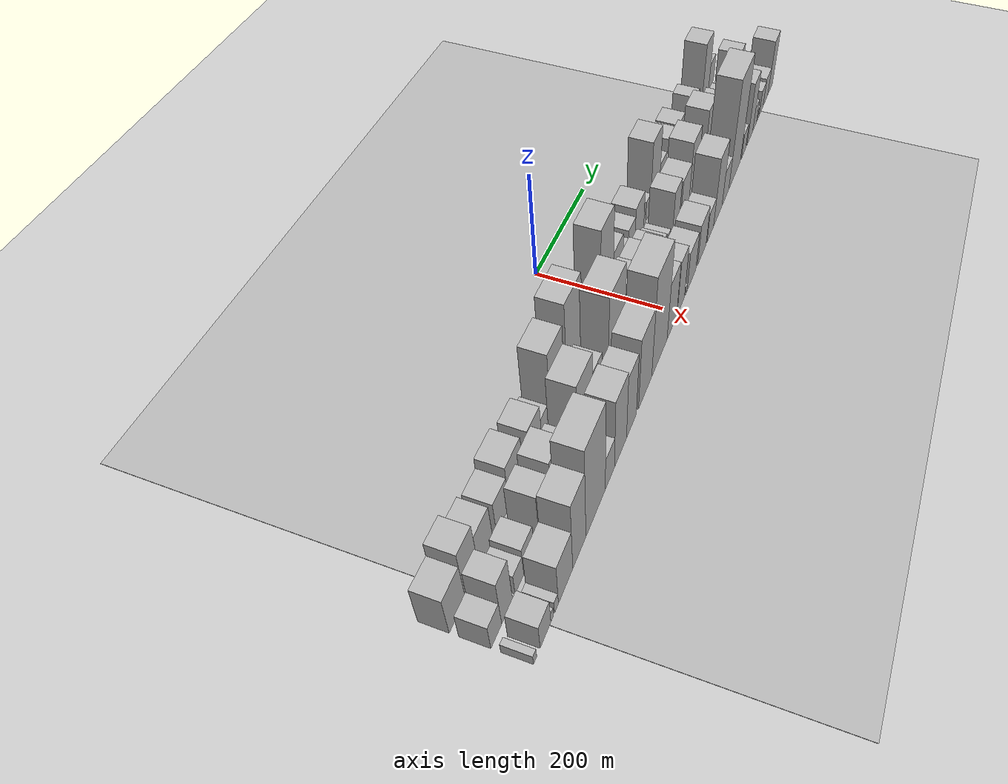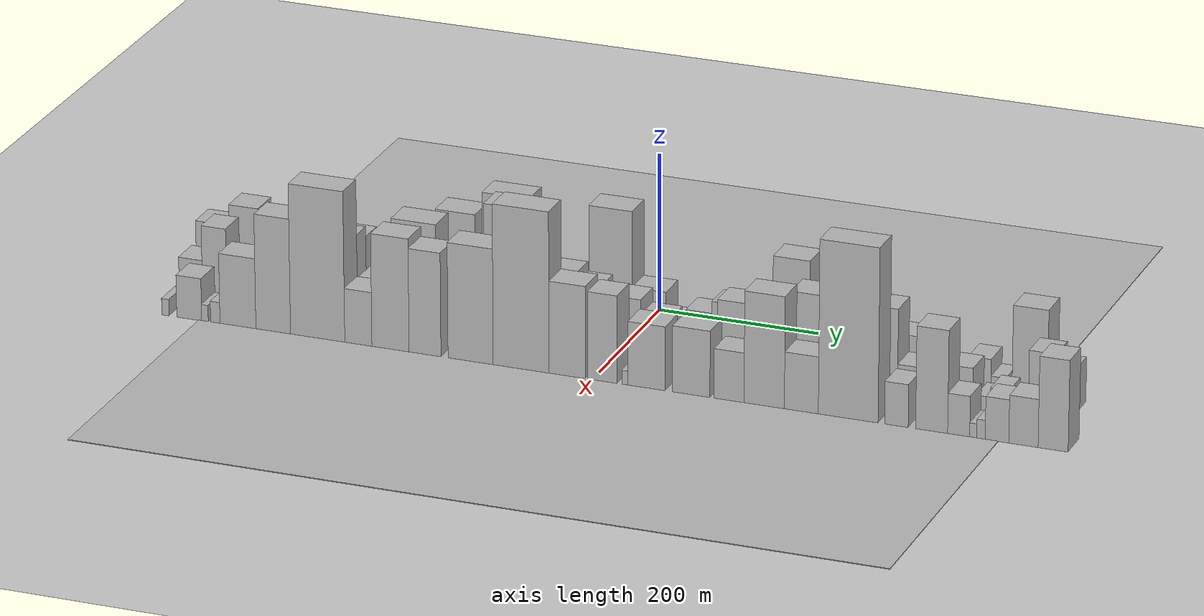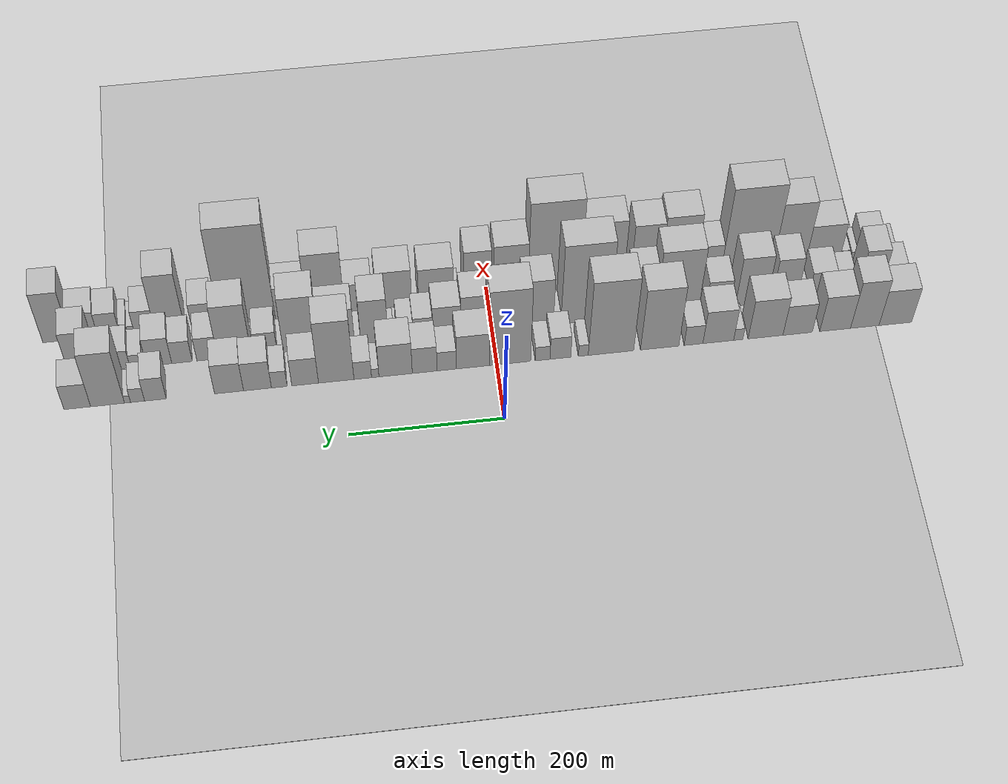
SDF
<?xml version="1.0" encoding="utf-8"?>

<sdf version="1.6">

   <world name="default">

      <gui fullscreen="0">

         <camera name="user_camera">

            <pose>-15 0 4.57585 0 0 0</pose>

            <view_controller>orbit</view_controller>

         </camera>

      </gui>

      <scene>

         <sky>

           <clouds>

             <speed>12</speed>

           </clouds>

         </sky>

         <ambient>0.4 0.4 0.4 1</ambient>

         <background>0.7 0.7 0.7 1</background>

         <shadows>1</shadows>

      </scene>

      <gravity>0 0 -9.8066</gravity>

      <magnetic_field>6e-06 2.3e-05 -4.2e-05</magnetic_field>

      <physics default="0" name="default_physics" type="ode">

         <ode>

            <solver>

               <type>quick</type>

               <iters>10</iters>

               <sor>1.0</sor>

               <use_dynamic_moi_rescaling>0</use_dynamic_moi_rescaling>

            </solver>

            <constraints>

               <cfm>0</cfm>

               <erp>0.2</erp>

               <contact_max_correcting_vel>100</contact_max_correcting_vel>

               <contact_surface_layer>0.001</contact_surface_layer>

            </constraints>

         </ode>

         <max_step_size>0.004</max_step_size>

         <real_time_factor>1</real_time_factor>

         <real_time_update_rate>250</real_time_update_rate>

      </physics>

      <light name="sun" type="directional">

         <cast_shadows>1</cast_shadows>

         <pose>0 0 10 0 0 0</pose>

         <diffuse>0.8 0.8 0.8 1</diffuse>

         <specular>0.2 0.2 0.2 1</specular>

         <attenuation>

            <range>1000</range>

            <constant>0.9</constant>

            <linear>0.01</linear>

            <quadratic>0.001</quadratic>

         </attenuation>

         <direction>-0.5 0.1 -0.9</direction>

      </light>

      <include>

         <name>ground_plane_1</name>

         <uri>model://HANNAS_ground_plane</uri>

         <pose>0 0 0  0 0 0</pose>

      </include>

      <include>

         <name>ground_plane_2</name>

         <uri>model://HANNAS_ground_plane</uri>

         <pose>100 0 0  0 0 0</pose>

      </include>

      <model name="building_1">

         <static>1</static>

         <pose frame="">100.0000 -526.1982 0 0.000000 0.000000 0.000000</pose>

         <link name="link">

            <pose frame="">0 0 40.50 0 0 0</pose>

            <collision name="collision">

               <geometry>

                  <box>

                     <size>40.0000 43.6035 81.0000</size>

                  </box>

               </geometry>

               <max_contacts>10</max_contacts>

               <surface>

                  <contact>

                     <ode/>

                  </contact>

                  <bounce/>

                  <friction>

                     <torsional>

                        <ode/>

                     </torsional>

                     <ode/>

                  </friction>

               </surface>

            </collision>

            <visual name="visual">

               <cast_shadows>0</cast_shadows>

               <geometry>

                  <box>

                     <size>40.0000 43.6035 81.0000</size>

                  </box>

               </geometry>

               <material>

                  <script>

                     <uri>model://HANNAS_wall/materials/scripts</uri>

                     <uri>model://HANNAS_wall/materials/textures</uri>

                     <name>vrc/HANNAS_wall</name>

                  </script>

               </material>

            </visual>

            <self_collide>0</self_collide>

            <enable_wind>0</enable_wind>

            <kinematic>0</kinematic>

         </link>

      </model>

      <model name="building_2">

         <static>1</static>

         <pose frame="">100.0000 -485.3963 0 0.000000 0.000000 0.000000</pose>

         <link name="link">

            <pose frame="">0 0 54.00 0 0 0</pose>

            <collision name="collision">

               <geometry>

                  <box>

                     <size>40.0000 38.0005 108.0000</size>

                  </box>

               </geometry>

               <max_contacts>10</max_contacts>

               <surface>

                  <contact>

                     <ode/>

                  </contact>

                  <bounce/>

                  <friction>

                     <torsional>

                        <ode/>

                     </torsional>

                     <ode/>

                  </friction>

               </surface>

            </collision>

            <visual name="visual">

               <cast_shadows>0</cast_shadows>

               <geometry>

                  <box>

                     <size>40.0000 38.0005 108.0000</size>

                  </box>

               </geometry>

               <material>

                  <script>

                     <uri>model://HANNAS_wall/materials/scripts</uri>

                     <uri>model://HANNAS_wall/materials/textures</uri>

                     <name>vrc/HANNAS_wall</name>

                  </script>

               </material>

            </visual>

            <self_collide>0</self_collide>

            <enable_wind>0</enable_wind>

            <kinematic>0</kinematic>

         </link>

      </model>

      <model name="building_3">

         <static>1</static>

         <pose frame="">100.0000 -445.8924 0 0.000000 0.000000 0.000000</pose>

         <link name="link">

            <pose frame="">0 0 40.50 0 0 0</pose>

            <collision name="collision">

               <geometry>

                  <box>

                     <size>40.0000 41.0073 81.0000</size>

                  </box>

               </geometry>

               <max_contacts>10</max_contacts>

               <surface>

                  <contact>

                     <ode/>

                  </contact>

                  <bounce/>

                  <friction>

                     <torsional>

                        <ode/>

                     </torsional>

                     <ode/>

                  </friction>

               </surface>

            </collision>

            <visual name="visual">

               <cast_shadows>0</cast_shadows>

               <geometry>

                  <box>

                     <size>40.0000 41.0073 81.0000</size>

                  </box>

               </geometry>

               <material>

                  <script>

                     <uri>model://HANNAS_wall/materials/scripts</uri>

                     <uri>model://HANNAS_wall/materials/textures</uri>

                     <name>vrc/HANNAS_wall</name>

                  </script>

               </material>

            </visual>

            <self_collide>0</self_collide>

            <enable_wind>0</enable_wind>

            <kinematic>0</kinematic>

         </link>

      </model>

      <model name="building_4">

         <static>1</static>

         <pose frame="">100.0000 -395.8718 0 0.000000 0.000000 0.000000</pose>

         <link name="link">

            <pose frame="">0 0 34.50 0 0 0</pose>

            <collision name="collision">

               <geometry>

                  <box>

                     <size>40.0000 39.0338 69.0000</size>

                  </box>

               </geometry>

               <max_contacts>10</max_contacts>

               <surface>

                  <contact>

                     <ode/>

                  </contact>

                  <bounce/>

                  <friction>

                     <torsional>

                        <ode/>

                     </torsional>

                     <ode/>

                  </friction>

               </surface>

            </collision>

            <visual name="visual">

               <cast_shadows>0</cast_shadows>

               <geometry>

                  <box>

                     <size>40.0000 39.0338 69.0000</size>

                  </box>

               </geometry>

               <material>

                  <script>

                     <uri>model://HANNAS_wall/materials/scripts</uri>

                     <uri>model://HANNAS_wall/materials/textures</uri>

                     <name>vrc/HANNAS_wall</name>

                  </script>

               </material>

            </visual>

            <self_collide>0</self_collide>

            <enable_wind>0</enable_wind>

            <kinematic>0</kinematic>

         </link>

      </model>

      <model name="building_5">

         <static>1</static>

         <pose frame="">100.0000 -353.2486 0 0.000000 0.000000 0.000000</pose>

         <link name="link">

            <pose frame="">0 0 45.00 0 0 0</pose>

            <collision name="collision">

               <geometry>

                  <box>

                     <size>40.0000 46.2126 90.0000</size>

                  </box>

               </geometry>

               <max_contacts>10</max_contacts>

               <surface>

                  <contact>

                     <ode/>

                  </contact>

                  <bounce/>

                  <friction>

                     <torsional>

                        <ode/>

                     </torsional>

                     <ode/>

                  </friction>

               </surface>

            </collision>

            <visual name="visual">

               <cast_shadows>0</cast_shadows>

               <geometry>

                  <box>

                     <size>40.0000 46.2126 90.0000</size>

                  </box>

               </geometry>

               <material>

                  <script>

                     <uri>model://HANNAS_wall/materials/scripts</uri>

                     <uri>model://HANNAS_wall/materials/textures</uri>

                     <name>vrc/HANNAS_wall</name>

                  </script>

               </material>

            </visual>

            <self_collide>0</self_collide>

            <enable_wind>0</enable_wind>

            <kinematic>0</kinematic>

         </link>

      </model>

      <model name="building_6">

         <static>1</static>

         <pose frame="">100.0000 -317.0287 0 0.000000 0.000000 0.000000</pose>

         <link name="link">

            <pose frame="">0 0 13.50 0 0 0</pose>

            <collision name="collision">

               <geometry>

                  <box>

                     <size>40.0000 12.2272 27.0000</size>

                  </box>

               </geometry>

               <max_contacts>10</max_contacts>

               <surface>

                  <contact>

                     <ode/>

                  </contact>

                  <bounce/>

                  <friction>

                     <torsional>

                        <ode/>

                     </torsional>

                     <ode/>

                  </friction>

               </surface>

            </collision>

            <visual name="visual">

               <cast_shadows>0</cast_shadows>

               <geometry>

                  <box>

                     <size>40.0000 12.2272 27.0000</size>

                  </box>

               </geometry>

               <material>

                  <script>

                     <uri>model://HANNAS_wall/materials/scripts</uri>

                     <uri>model://HANNAS_wall/materials/textures</uri>

                     <name>vrc/HANNAS_wall</name>

                  </script>

               </material>

            </visual>

            <self_collide>0</self_collide>

            <enable_wind>0</enable_wind>

            <kinematic>0</kinematic>

         </link>

      </model>

      <model name="building_7">

         <static>1</static>

         <pose frame="">100.0000 -290.6172 0 0.000000 0.000000 0.000000</pose>

         <link name="link">

            <pose frame="">0 0 37.50 0 0 0</pose>

            <collision name="collision">

               <geometry>

                  <box>

                     <size>40.0000 40.5959 75.0000</size>

                  </box>

               </geometry>

               <max_contacts>10</max_contacts>

               <surface>

                  <contact>

                     <ode/>

                  </contact>

                  <bounce/>

                  <friction>

                     <torsional>

                        <ode/>

                     </torsional>

                     <ode/>

                  </friction>

               </surface>

            </collision>

            <visual name="visual">

               <cast_shadows>0</cast_shadows>

               <geometry>

                  <box>

                     <size>40.0000 40.5959 75.0000</size>

                  </box>

               </geometry>

               <material>

                  <script>

                     <uri>model://HANNAS_wall/materials/scripts</uri>

                     <uri>model://HANNAS_wall/materials/textures</uri>

                     <name>vrc/HANNAS_wall</name>

                  </script>

               </material>

            </visual>

            <self_collide>0</self_collide>

            <enable_wind>0</enable_wind>

            <kinematic>0</kinematic>

         </link>

      </model>

      <model name="building_8">

         <static>1</static>

         <pose frame="">100.0000 -257.9025 0 0.000000 0.000000 0.000000</pose>

         <link name="link">

            <pose frame="">0 0 22.50 0 0 0</pose>

            <collision name="collision">

               <geometry>

                  <box>

                     <size>40.0000 24.8334 45.0000</size>

                  </box>

               </geometry>

               <max_contacts>10</max_contacts>

               <surface>

                  <contact>

                     <ode/>

                  </contact>

                  <bounce/>

                  <friction>

                     <torsional>

                        <ode/>

                     </torsional>

                     <ode/>

                  </friction>

               </surface>

            </collision>

            <visual name="visual">

               <cast_shadows>0</cast_shadows>

               <geometry>

                  <box>

                     <size>40.0000 24.8334 45.0000</size>

                  </box>

               </geometry>

               <material>

                  <script>

                     <uri>model://HANNAS_wall/materials/scripts</uri>

                     <uri>model://HANNAS_wall/materials/textures</uri>

                     <name>vrc/HANNAS_wall</name>

                  </script>

               </material>

            </visual>

            <self_collide>0</self_collide>

            <enable_wind>0</enable_wind>

            <kinematic>0</kinematic>

         </link>

      </model>

      <model name="building_9">

         <static>1</static>

         <pose frame="">100.0000 -213.2103 0 0.000000 0.000000 0.000000</pose>

         <link name="link">

            <pose frame="">0 0 70.50 0 0 0</pose>

            <collision name="collision">

               <geometry>

                  <box>

                     <size>40.0000 50.5510 141.0000</size>

                  </box>

               </geometry>

               <max_contacts>10</max_contacts>

               <surface>

                  <contact>

                     <ode/>

                  </contact>

                  <bounce/>

                  <friction>

                     <torsional>

                        <ode/>

                     </torsional>

                     <ode/>

                  </friction>

               </surface>

            </collision>

            <visual name="visual">

               <cast_shadows>0</cast_shadows>

               <geometry>

                  <box>

                     <size>40.0000 50.5510 141.0000</size>

                  </box>

               </geometry>

               <material>

                  <script>

                     <uri>model://HANNAS_wall/materials/scripts</uri>

                     <uri>model://HANNAS_wall/materials/textures</uri>

                     <name>vrc/HANNAS_wall</name>

                  </script>

               </material>

            </visual>

            <self_collide>0</self_collide>

            <enable_wind>0</enable_wind>

            <kinematic>0</kinematic>

         </link>

      </model>

      <model name="building_10">

         <static>1</static>

         <pose frame="">100.0000 -149.0451 0 0.000000 0.000000 0.000000</pose>

         <link name="link">

            <pose frame="">0 0 85.50 0 0 0</pose>

            <collision name="collision">

               <geometry>

                  <box>

                     <size>40.0000 59.7794 171.0000</size>

                  </box>

               </geometry>

               <max_contacts>10</max_contacts>

               <surface>

                  <contact>

                     <ode/>

                  </contact>

                  <bounce/>

                  <friction>

                     <torsional>

                        <ode/>

                     </torsional>

                     <ode/>

                  </friction>

               </surface>

            </collision>

            <visual name="visual">

               <cast_shadows>0</cast_shadows>

               <geometry>

                  <box>

                     <size>40.0000 59.7794 171.0000</size>

                  </box>

               </geometry>

               <material>

                  <script>

                     <uri>model://HANNAS_wall/materials/scripts</uri>

                     <uri>model://HANNAS_wall/materials/textures</uri>

                     <name>vrc/HANNAS_wall</name>

                  </script>

               </material>

            </visual>

            <self_collide>0</self_collide>

            <enable_wind>0</enable_wind>

            <kinematic>0</kinematic>

         </link>

      </model>

      <model name="building_11">

         <static>1</static>

         <pose frame="">100.0000 -112.6916 0 0.000000 0.000000 0.000000</pose>

         <link name="link">

            <pose frame="">0 0 13.50 0 0 0</pose>

            <collision name="collision">

               <geometry>

                  <box>

                     <size>40.0000 12.9276 27.0000</size>

                  </box>

               </geometry>

               <max_contacts>10</max_contacts>

               <surface>

                  <contact>

                     <ode/>

                  </contact>

                  <bounce/>

                  <friction>

                     <torsional>

                        <ode/>

                     </torsional>

                     <ode/>

                  </friction>

               </surface>

            </collision>

            <visual name="visual">

               <cast_shadows>0</cast_shadows>

               <geometry>

                  <box>

                     <size>40.0000 12.9276 27.0000</size>

                  </box>

               </geometry>

               <material>

                  <script>

                     <uri>model://HANNAS_wall/materials/scripts</uri>

                     <uri>model://HANNAS_wall/materials/textures</uri>

                     <name>vrc/HANNAS_wall</name>

                  </script>

               </material>

            </visual>

            <self_collide>0</self_collide>

            <enable_wind>0</enable_wind>

            <kinematic>0</kinematic>

         </link>

      </model>

      <model name="building_12">

         <static>1</static>

         <pose frame="">100.0000 -82.6080 0 0.000000 0.000000 0.000000</pose>

         <link name="link">

            <pose frame="">0 0 25.50 0 0 0</pose>

            <collision name="collision">

               <geometry>

                  <box>

                     <size>40.0000 27.2396 51.0000</size>

                  </box>

               </geometry>

               <max_contacts>10</max_contacts>

               <surface>

                  <contact>

                     <ode/>

                  </contact>

                  <bounce/>

                  <friction>

                     <torsional>

                        <ode/>

                     </torsional>

                     <ode/>

                  </friction>

               </surface>

            </collision>

            <visual name="visual">

               <cast_shadows>0</cast_shadows>

               <geometry>

                  <box>

                     <size>40.0000 27.2396 51.0000</size>

                  </box>

               </geometry>

               <material>

                  <script>

                     <uri>model://HANNAS_wall/materials/scripts</uri>

                     <uri>model://HANNAS_wall/materials/textures</uri>

                     <name>vrc/HANNAS_wall</name>

                  </script>

               </material>

            </visual>

            <self_collide>0</self_collide>

            <enable_wind>0</enable_wind>

            <kinematic>0</kinematic>

         </link>

      </model>

      <model name="building_13">

         <static>1</static>

         <pose frame="">100.0000 -59.3566 0 0.000000 0.000000 0.000000</pose>

         <link name="link">

            <pose frame="">0 0 16.50 0 0 0</pose>

            <collision name="collision">

               <geometry>

                  <box>

                     <size>40.0000 19.2632 33.0000</size>

                  </box>

               </geometry>

               <max_contacts>10</max_contacts>

               <surface>

                  <contact>

                     <ode/>

                  </contact>

                  <bounce/>

                  <friction>

                     <torsional>

                        <ode/>

                     </torsional>

                     <ode/>

                  </friction>

               </surface>

            </collision>

            <visual name="visual">

               <cast_shadows>0</cast_shadows>

               <geometry>

                  <box>

                     <size>40.0000 19.2632 33.0000</size>

                  </box>

               </geometry>

               <material>

                  <script>

                     <uri>model://HANNAS_wall/materials/scripts</uri>

                     <uri>model://HANNAS_wall/materials/textures</uri>

                     <name>vrc/HANNAS_wall</name>

                  </script>

               </material>

            </visual>

            <self_collide>0</self_collide>

            <enable_wind>0</enable_wind>

            <kinematic>0</kinematic>

         </link>

      </model>

      <model name="building_14">

         <static>1</static>

         <pose frame="">100.0000 -16.7915 0 0.000000 0.000000 0.000000</pose>

         <link name="link">

            <pose frame="">0 0 87.00 0 0 0</pose>

            <collision name="collision">

               <geometry>

                  <box>

                     <size>40.0000 53.8670 174.0000</size>

                  </box>

               </geometry>

               <max_contacts>10</max_contacts>

               <surface>

                  <contact>

                     <ode/>

                  </contact>

                  <bounce/>

                  <friction>

                     <torsional>

                        <ode/>

                     </torsional>

                     <ode/>

                  </friction>

               </surface>

            </collision>

            <visual name="visual">

               <cast_shadows>0</cast_shadows>

               <geometry>

                  <box>

                     <size>40.0000 53.8670 174.0000</size>

                  </box>

               </geometry>

               <material>

                  <script>

                     <uri>model://HANNAS_wall/materials/scripts</uri>

                     <uri>model://HANNAS_wall/materials/textures</uri>

                     <name>vrc/HANNAS_wall</name>

                  </script>

               </material>

            </visual>

            <self_collide>0</self_collide>

            <enable_wind>0</enable_wind>

            <kinematic>0</kinematic>

         </link>

      </model>

      <model name="building_15">

         <static>1</static>

         <pose frame="">100.0000 31.6041 0 0.000000 0.000000 0.000000</pose>

         <link name="link">

            <pose frame="">0 0 39.00 0 0 0</pose>

            <collision name="collision">

               <geometry>

                  <box>

                     <size>40.0000 42.9242 78.0000</size>

                  </box>

               </geometry>

               <max_contacts>10</max_contacts>

               <surface>

                  <contact>

                     <ode/>

                  </contact>

                  <bounce/>

                  <friction>

                     <torsional>

                        <ode/>

                     </torsional>

                     <ode/>

                  </friction>

               </surface>

            </collision>

            <visual name="visual">

               <cast_shadows>0</cast_shadows>

               <geometry>

                  <box>

                     <size>40.0000 42.9242 78.0000</size>

                  </box>

               </geometry>

               <material>

                  <script>

                     <uri>model://HANNAS_wall/materials/scripts</uri>

                     <uri>model://HANNAS_wall/materials/textures</uri>

                     <name>vrc/HANNAS_wall</name>

                  </script>

               </material>

            </visual>

            <self_collide>0</self_collide>

            <enable_wind>0</enable_wind>

            <kinematic>0</kinematic>

         </link>

      </model>

      <model name="building_16">

         <static>1</static>

         <pose frame="">100.0000 65.6419 0 0.000000 0.000000 0.000000</pose>

         <link name="link">

            <pose frame="">0 0 22.50 0 0 0</pose>

            <collision name="collision">

               <geometry>

                  <box>

                     <size>40.0000 25.1513 45.0000</size>

                  </box>

               </geometry>

               <max_contacts>10</max_contacts>

               <surface>

                  <contact>

                     <ode/>

                  </contact>

                  <bounce/>

                  <friction>

                     <torsional>

                        <ode/>

                     </torsional>

                     <ode/>

                  </friction>

               </surface>

            </collision>

            <visual name="visual">

               <cast_shadows>0</cast_shadows>

               <geometry>

                  <box>

                     <size>40.0000 25.1513 45.0000</size>

                  </box>

               </geometry>

               <material>

                  <script>

                     <uri>model://HANNAS_wall/materials/scripts</uri>

                     <uri>model://HANNAS_wall/materials/textures</uri>

                     <name>vrc/HANNAS_wall</name>

                  </script>

               </material>

            </visual>

            <self_collide>0</self_collide>

            <enable_wind>0</enable_wind>

            <kinematic>0</kinematic>

         </link>

      </model>

      <model name="building_17">

         <static>1</static>

         <pose frame="">100.0000 94.3619 0 0.000000 0.000000 0.000000</pose>

         <link name="link">

            <pose frame="">0 0 30.00 0 0 0</pose>

            <collision name="collision">

               <geometry>

                  <box>

                     <size>40.0000 32.2888 60.0000</size>

                  </box>

               </geometry>

               <max_contacts>10</max_contacts>

               <surface>

                  <contact>

                     <ode/>

                  </contact>

                  <bounce/>

                  <friction>

                     <torsional>

                        <ode/>

                     </torsional>

                     <ode/>

                  </friction>

               </surface>

            </collision>

            <visual name="visual">

               <cast_shadows>0</cast_shadows>

               <geometry>

                  <box>

                     <size>40.0000 32.2888 60.0000</size>

                  </box>

               </geometry>

               <material>

                  <script>

                     <uri>model://HANNAS_wall/materials/scripts</uri>

                     <uri>model://HANNAS_wall/materials/textures</uri>

                     <name>vrc/HANNAS_wall</name>

                  </script>

               </material>

            </visual>

            <self_collide>0</self_collide>

            <enable_wind>0</enable_wind>

            <kinematic>0</kinematic>

         </link>

      </model>

      <model name="building_18">

         <static>1</static>

         <pose frame="">100.0000 132.1816 0 0.000000 0.000000 0.000000</pose>

         <link name="link">

            <pose frame="">0 0 37.50 0 0 0</pose>

            <collision name="collision">

               <geometry>

                  <box>

                     <size>40.0000 43.3505 75.0000</size>

                  </box>

               </geometry>

               <max_contacts>10</max_contacts>

               <surface>

                  <contact>

                     <ode/>

                  </contact>

                  <bounce/>

                  <friction>

                     <torsional>

                        <ode/>

                     </torsional>

                     <ode/>

                  </friction>

               </surface>

            </collision>

            <visual name="visual">

               <cast_shadows>0</cast_shadows>

               <geometry>

                  <box>

                     <size>40.0000 43.3505 75.0000</size>

                  </box>

               </geometry>

               <material>

                  <script>

                     <uri>model://HANNAS_wall/materials/scripts</uri>

                     <uri>model://HANNAS_wall/materials/textures</uri>

                     <name>vrc/HANNAS_wall</name>

                  </script>

               </material>

            </visual>

            <self_collide>0</self_collide>

            <enable_wind>0</enable_wind>

            <kinematic>0</kinematic>

         </link>

      </model>

      <model name="building_19">

         <static>1</static>

         <pose frame="">100.0000 158.6181 0 0.000000 0.000000 0.000000</pose>

         <link name="link">

            <pose frame="">0 0 10.50 0 0 0</pose>

            <collision name="collision">

               <geometry>

                  <box>

                     <size>40.0000 9.5225 21.0000</size>

                  </box>

               </geometry>

               <max_contacts>10</max_contacts>

               <surface>

                  <contact>

                     <ode/>

                  </contact>

                  <bounce/>

                  <friction>

                     <torsional>

                        <ode/>

                     </torsional>

                     <ode/>

                  </friction>

               </surface>

            </collision>

            <visual name="visual">

               <cast_shadows>0</cast_shadows>

               <geometry>

                  <box>

                     <size>40.0000 9.5225 21.0000</size>

                  </box>

               </geometry>

               <material>

                  <script>

                     <uri>model://HANNAS_wall/materials/scripts</uri>

                     <uri>model://HANNAS_wall/materials/textures</uri>

                     <name>vrc/HANNAS_wall</name>

                  </script>

               </material>

            </visual>

            <self_collide>0</self_collide>

            <enable_wind>0</enable_wind>

            <kinematic>0</kinematic>

         </link>

      </model>

      <model name="building_20">

         <static>1</static>

         <pose frame="">100.0000 174.7911 0 0.000000 0.000000 0.000000</pose>

         <link name="link">

            <pose frame="">0 0 21.00 0 0 0</pose>

            <collision name="collision">

               <geometry>

                  <box>

                     <size>40.0000 22.8234 42.0000</size>

                  </box>

               </geometry>

               <max_contacts>10</max_contacts>

               <surface>

                  <contact>

                     <ode/>

                  </contact>

                  <bounce/>

                  <friction>

                     <torsional>

                        <ode/>

                     </torsional>

                     <ode/>

                  </friction>

               </surface>

            </collision>

            <visual name="visual">

               <cast_shadows>0</cast_shadows>

               <geometry>

                  <box>

                     <size>40.0000 22.8234 42.0000</size>

                  </box>

               </geometry>

               <material>

                  <script>

                     <uri>model://HANNAS_wall/materials/scripts</uri>

                     <uri>model://HANNAS_wall/materials/textures</uri>

                     <name>vrc/HANNAS_wall</name>

                  </script>

               </material>

            </visual>

            <self_collide>0</self_collide>

            <enable_wind>0</enable_wind>

            <kinematic>0</kinematic>

         </link>

      </model>

      <model name="building_21">

         <static>1</static>

         <pose frame="">100.0000 209.1163 0 0.000000 0.000000 0.000000</pose>

         <link name="link">

            <pose frame="">0 0 72.00 0 0 0</pose>

            <collision name="collision">

               <geometry>

                  <box>

                     <size>40.0000 45.8270 144.0000</size>

                  </box>

               </geometry>

               <max_contacts>10</max_contacts>

               <surface>

                  <contact>

                     <ode/>

                  </contact>

                  <bounce/>

                  <friction>

                     <torsional>

                        <ode/>

                     </torsional>

                     <ode/>

                  </friction>

               </surface>

            </collision>

            <visual name="visual">

               <cast_shadows>0</cast_shadows>

               <geometry>

                  <box>

                     <size>40.0000 45.8270 144.0000</size>

                  </box>

               </geometry>

               <material>

                  <script>

                     <uri>model://HANNAS_wall/materials/scripts</uri>

                     <uri>model://HANNAS_wall/materials/textures</uri>

                     <name>vrc/HANNAS_wall</name>

                  </script>

               </material>

            </visual>

            <self_collide>0</self_collide>

            <enable_wind>0</enable_wind>

            <kinematic>0</kinematic>

         </link>

      </model>

      <model name="building_22">

         <static>1</static>

         <pose frame="">100.0000 249.2329 0 0.000000 0.000000 0.000000</pose>

         <link name="link">

            <pose frame="">0 0 31.50 0 0 0</pose>

            <collision name="collision">

               <geometry>

                  <box>

                     <size>40.0000 34.4062 63.0000</size>

                  </box>

               </geometry>

               <max_contacts>10</max_contacts>

               <surface>

                  <contact>

                     <ode/>

                  </contact>

                  <bounce/>

                  <friction>

                     <torsional>

                        <ode/>

                     </torsional>

                     <ode/>

                  </friction>

               </surface>

            </collision>

            <visual name="visual">

               <cast_shadows>0</cast_shadows>

               <geometry>

                  <box>

                     <size>40.0000 34.4062 63.0000</size>

                  </box>

               </geometry>

               <material>

                  <script>

                     <uri>model://HANNAS_wall/materials/scripts</uri>

                     <uri>model://HANNAS_wall/materials/textures</uri>

                     <name>vrc/HANNAS_wall</name>

                  </script>

               </material>

            </visual>

            <self_collide>0</self_collide>

            <enable_wind>0</enable_wind>

            <kinematic>0</kinematic>

         </link>

      </model>

      <model name="building_23">

         <static>1</static>

         <pose frame="">100.0000 282.5819 0 0.000000 0.000000 0.000000</pose>

         <link name="link">

            <pose frame="">0 0 19.50 0 0 0</pose>

            <collision name="collision">

               <geometry>

                  <box>

                     <size>40.0000 20.2919 39.0000</size>

                  </box>

               </geometry>

               <max_contacts>10</max_contacts>

               <surface>

                  <contact>

                     <ode/>

                  </contact>

                  <bounce/>

                  <friction>

                     <torsional>

                        <ode/>

                     </torsional>

                     <ode/>

                  </friction>

               </surface>

            </collision>

            <visual name="visual">

               <cast_shadows>0</cast_shadows>

               <geometry>

                  <box>

                     <size>40.0000 20.2919 39.0000</size>

                  </box>

               </geometry>

               <material>

                  <script>

                     <uri>model://HANNAS_wall/materials/scripts</uri>

                     <uri>model://HANNAS_wall/materials/textures</uri>

                     <name>vrc/HANNAS_wall</name>

                  </script>

               </material>

            </visual>

            <self_collide>0</self_collide>

            <enable_wind>0</enable_wind>

            <kinematic>0</kinematic>

         </link>

      </model>

      <model name="building_24">

         <static>1</static>

         <pose frame="">100.0000 310.7004 0 0.000000 0.000000 0.000000</pose>

         <link name="link">

            <pose frame="">0 0 33.00 0 0 0</pose>

            <collision name="collision">

               <geometry>

                  <box>

                     <size>40.0000 35.9451 66.0000</size>

                  </box>

               </geometry>

               <max_contacts>10</max_contacts>

               <surface>

                  <contact>

                     <ode/>

                  </contact>

                  <bounce/>

                  <friction>

                     <torsional>

                        <ode/>

                     </torsional>

                     <ode/>

                  </friction>

               </surface>

            </collision>

            <visual name="visual">

               <cast_shadows>0</cast_shadows>

               <geometry>

                  <box>

                     <size>40.0000 35.9451 66.0000</size>

                  </box>

               </geometry>

               <material>

                  <script>

                     <uri>model://HANNAS_wall/materials/scripts</uri>

                     <uri>model://HANNAS_wall/materials/textures</uri>

                     <name>vrc/HANNAS_wall</name>

                  </script>

               </material>

            </visual>

            <self_collide>0</self_collide>

            <enable_wind>0</enable_wind>

            <kinematic>0</kinematic>

         </link>

      </model>

      <model name="building_25">

         <static>1</static>

         <pose frame="">100.0000 347.2897 0 0.000000 0.000000 0.000000</pose>

         <link name="link">

            <pose frame="">0 0 34.50 0 0 0</pose>

            <collision name="collision">

               <geometry>

                  <box>

                     <size>40.0000 37.2335 69.0000</size>

                  </box>

               </geometry>

               <max_contacts>10</max_contacts>

               <surface>

                  <contact>

                     <ode/>

                  </contact>

                  <bounce/>

                  <friction>

                     <torsional>

                        <ode/>

                     </torsional>

                     <ode/>

                  </friction>

               </surface>

            </collision>

            <visual name="visual">

               <cast_shadows>0</cast_shadows>

               <geometry>

                  <box>

                     <size>40.0000 37.2335 69.0000</size>

                  </box>

               </geometry>

               <material>

                  <script>

                     <uri>model://HANNAS_wall/materials/scripts</uri>

                     <uri>model://HANNAS_wall/materials/textures</uri>

                     <name>vrc/HANNAS_wall</name>

                  </script>

               </material>

            </visual>

            <self_collide>0</self_collide>

            <enable_wind>0</enable_wind>

            <kinematic>0</kinematic>

         </link>

      </model>

      <model name="building_26">

         <static>1</static>

         <pose frame="">100.0000 441.6426 0 0.000000 0.000000 0.000000</pose>

         <link name="link">

            <pose frame="">0 0 27.00 0 0 0</pose>

            <collision name="collision">

               <geometry>

                  <box>

                     <size>40.0000 27.8241 54.0000</size>

                  </box>

               </geometry>

               <max_contacts>10</max_contacts>

               <surface>

                  <contact>

                     <ode/>

                  </contact>

                  <bounce/>

                  <friction>

                     <torsional>

                        <ode/>

                     </torsional>

                     <ode/>

                  </friction>

               </surface>

            </collision>

            <visual name="visual">

               <cast_shadows>0</cast_shadows>

               <geometry>

                  <box>

                     <size>40.0000 27.8241 54.0000</size>

                  </box>

               </geometry>

               <material>

                  <script>

                     <uri>model://HANNAS_wall/materials/scripts</uri>

                     <uri>model://HANNAS_wall/materials/textures</uri>

                     <name>vrc/HANNAS_wall</name>

                  </script>

               </material>

            </visual>

            <self_collide>0</self_collide>

            <enable_wind>0</enable_wind>

            <kinematic>0</kinematic>

         </link>

      </model>

      <model name="building_27">

         <static>1</static>

         <pose frame="">100.0000 464.5478 0 0.000000 0.000000 0.000000</pose>

         <link name="link">

            <pose frame="">0 0 16.50 0 0 0</pose>

            <collision name="collision">

               <geometry>

                  <box>

                     <size>40.0000 17.9862 33.0000</size>

                  </box>

               </geometry>

               <max_contacts>10</max_contacts>

               <surface>

                  <contact>

                     <ode/>

                  </contact>

                  <bounce/>

                  <friction>

                     <torsional>

                        <ode/>

                     </torsional>

                     <ode/>

                  </friction>

               </surface>

            </collision>

            <visual name="visual">

               <cast_shadows>0</cast_shadows>

               <geometry>

                  <box>

                     <size>40.0000 17.9862 33.0000</size>

                  </box>

               </geometry>

               <material>

                  <script>

                     <uri>model://HANNAS_wall/materials/scripts</uri>

                     <uri>model://HANNAS_wall/materials/textures</uri>

                     <name>vrc/HANNAS_wall</name>

                  </script>

               </material>

            </visual>

            <self_collide>0</self_collide>

            <enable_wind>0</enable_wind>

            <kinematic>0</kinematic>

         </link>

      </model>

      <model name="building_28">

         <static>1</static>

         <pose frame="">100.0000 477.3907 0 0.000000 0.000000 0.000000</pose>

         <link name="link">

            <pose frame="">0 0 9.00 0 0 0</pose>

            <collision name="collision">

               <geometry>

                  <box>

                     <size>40.0000 7.6996 18.0000</size>

                  </box>

               </geometry>

               <max_contacts>10</max_contacts>

               <surface>

                  <contact>

                     <ode/>

                  </contact>

                  <bounce/>

                  <friction>

                     <torsional>

                        <ode/>

                     </torsional>

                     <ode/>

                  </friction>

               </surface>

            </collision>

            <visual name="visual">

               <cast_shadows>0</cast_shadows>

               <geometry>

                  <box>

                     <size>40.0000 7.6996 18.0000</size>

                  </box>

               </geometry>

               <material>

                  <script>

                     <uri>model://HANNAS_wall/materials/scripts</uri>

                     <uri>model://HANNAS_wall/materials/textures</uri>

                     <name>vrc/HANNAS_wall</name>

                  </script>

               </material>

            </visual>

            <self_collide>0</self_collide>

            <enable_wind>0</enable_wind>

            <kinematic>0</kinematic>

         </link>

      </model>

      <model name="building_29">

         <static>1</static>

         <pose frame="">100.0000 502.8039 0 0.000000 0.000000 0.000000</pose>

         <link name="link">

            <pose frame="">0 0 63.00 0 0 0</pose>

            <collision name="collision">

               <geometry>

                  <box>

                     <size>40.0000 43.1269 126.0000</size>

                  </box>

               </geometry>

               <max_contacts>10</max_contacts>

               <surface>

                  <contact>

                     <ode/>

                  </contact>

                  <bounce/>

                  <friction>

                     <torsional>

                        <ode/>

                     </torsional>

                     <ode/>

                  </friction>

               </surface>

            </collision>

            <visual name="visual">

               <cast_shadows>0</cast_shadows>

               <geometry>

                  <box>

                     <size>40.0000 43.1269 126.0000</size>

                  </box>

               </geometry>

               <material>

                  <script>

                     <uri>model://HANNAS_wall/materials/scripts</uri>

                     <uri>model://HANNAS_wall/materials/textures</uri>

                     <name>vrc/HANNAS_wall</name>

                  </script>

               </material>

            </visual>

            <self_collide>0</self_collide>

            <enable_wind>0</enable_wind>

            <kinematic>0</kinematic>

         </link>

      </model>

      <model name="building_30">

         <static>1</static>

         <pose frame="">100.0000 541.4067 0 0.000000 0.000000 0.000000</pose>

         <link name="link">

            <pose frame="">0 0 28.50 0 0 0</pose>

            <collision name="collision">

               <geometry>

                  <box>

                     <size>40.0000 34.0788 57.0000</size>

                  </box>

               </geometry>

               <max_contacts>10</max_contacts>

               <surface>

                  <contact>

                     <ode/>

                  </contact>

                  <bounce/>

                  <friction>

                     <torsional>

                        <ode/>

                     </torsional>

                     <ode/>

                  </friction>

               </surface>

            </collision>

            <visual name="visual">

               <cast_shadows>0</cast_shadows>

               <geometry>

                  <box>

                     <size>40.0000 34.0788 57.0000</size>

                  </box>

               </geometry>

               <material>

                  <script>

                     <uri>model://HANNAS_wall/materials/scripts</uri>

                     <uri>model://HANNAS_wall/materials/textures</uri>

                     <name>vrc/HANNAS_wall</name>

                  </script>

               </material>

            </visual>

            <self_collide>0</self_collide>

            <enable_wind>0</enable_wind>

            <kinematic>0</kinematic>

         </link>

      </model>

      <model name="building_31">

         <static>1</static>

         <pose frame="">152.0000 -532.8554 0 0.000000 0.000000 0.000000</pose>

         <link name="link">

            <pose frame="">0 0 27.00 0 0 0</pose>

            <collision name="collision">

               <geometry>

                  <box>

                     <size>40.0000 30.2892 54.0000</size>

                  </box>

               </geometry>

               <max_contacts>10</max_contacts>

               <surface>

                  <contact>

                     <ode/>

                  </contact>

                  <bounce/>

                  <friction>

                     <torsional>

                        <ode/>

                     </torsional>

                     <ode/>

                  </friction>

               </surface>

            </collision>

            <visual name="visual">

               <cast_shadows>0</cast_shadows>

               <geometry>

                  <box>

                     <size>40.0000 30.2892 54.0000</size>

                  </box>

               </geometry>

               <material>

                  <script>

                     <uri>model://HANNAS_wall/materials/scripts</uri>

                     <uri>model://HANNAS_wall/materials/textures</uri>

                     <name>vrc/HANNAS_wall</name>

                  </script>

               </material>

            </visual>

            <self_collide>0</self_collide>

            <enable_wind>0</enable_wind>

            <kinematic>0</kinematic>

         </link>

      </model>

      <model name="building_32">

         <static>1</static>

         <pose frame="">152.0000 -502.0154 0 0.000000 0.000000 0.000000</pose>

         <link name="link">

            <pose frame="">0 0 49.50 0 0 0</pose>

            <collision name="collision">

               <geometry>

                  <box>

                     <size>40.0000 31.3909 99.0000</size>

                  </box>

               </geometry>

               <max_contacts>10</max_contacts>

               <surface>

                  <contact>

                     <ode/>

                  </contact>

                  <bounce/>

                  <friction>

                     <torsional>

                        <ode/>

                     </torsional>

                     <ode/>

                  </friction>

               </surface>

            </collision>

            <visual name="visual">

               <cast_shadows>0</cast_shadows>

               <geometry>

                  <box>

                     <size>40.0000 31.3909 99.0000</size>

                  </box>

               </geometry>

               <material>

                  <script>

                     <uri>model://HANNAS_wall/materials/scripts</uri>

                     <uri>model://HANNAS_wall/materials/textures</uri>

                     <name>vrc/HANNAS_wall</name>

                  </script>

               </material>

            </visual>

            <self_collide>0</self_collide>

            <enable_wind>0</enable_wind>

            <kinematic>0</kinematic>

         </link>

      </model>

      <model name="building_33">

         <static>1</static>

         <pose frame="">152.0000 -466.1909 0 0.000000 0.000000 0.000000</pose>

         <link name="link">

            <pose frame="">0 0 22.50 0 0 0</pose>

            <collision name="collision">

               <geometry>

                  <box>

                     <size>40.0000 26.2582 45.0000</size>

                  </box>

               </geometry>

               <max_contacts>10</max_contacts>

               <surface>

                  <contact>

                     <ode/>

                  </contact>

                  <bounce/>

                  <friction>

                     <torsional>

                        <ode/>

                     </torsional>

                     <ode/>

                  </friction>

               </surface>

            </collision>

            <visual name="visual">

               <cast_shadows>0</cast_shadows>

               <geometry>

                  <box>

                     <size>40.0000 26.2582 45.0000</size>

                  </box>

               </geometry>

               <material>

                  <script>

                     <uri>model://HANNAS_wall/materials/scripts</uri>

                     <uri>model://HANNAS_wall/materials/textures</uri>

                     <name>vrc/HANNAS_wall</name>

                  </script>

               </material>

            </visual>

            <self_collide>0</self_collide>

            <enable_wind>0</enable_wind>

            <kinematic>0</kinematic>

         </link>

      </model>

      <model name="building_34">

         <static>1</static>

         <pose frame="">152.0000 -436.7040 0 0.000000 0.000000 0.000000</pose>

         <link name="link">

            <pose frame="">0 0 30.00 0 0 0</pose>

            <collision name="collision">

               <geometry>

                  <box>

                     <size>40.0000 32.7156 60.0000</size>

                  </box>

               </geometry>

               <max_contacts>10</max_contacts>

               <surface>

                  <contact>

                     <ode/>

                  </contact>

                  <bounce/>

                  <friction>

                     <torsional>

                        <ode/>

                     </torsional>

                     <ode/>

                  </friction>

               </surface>

            </collision>

            <visual name="visual">

               <cast_shadows>0</cast_shadows>

               <geometry>

                  <box>

                     <size>40.0000 32.7156 60.0000</size>

                  </box>

               </geometry>

               <material>

                  <script>

                     <uri>model://HANNAS_wall/materials/scripts</uri>

                     <uri>model://HANNAS_wall/materials/textures</uri>

                     <name>vrc/HANNAS_wall</name>

                  </script>

               </material>

            </visual>

            <self_collide>0</self_collide>

            <enable_wind>0</enable_wind>

            <kinematic>0</kinematic>

         </link>

      </model>

      <model name="building_35">

         <static>1</static>

         <pose frame="">152.0000 -416.1719 0 0.000000 0.000000 0.000000</pose>

         <link name="link">

            <pose frame="">0 0 9.00 0 0 0</pose>

            <collision name="collision">

               <geometry>

                  <box>

                     <size>40.0000 8.3486 18.0000</size>

                  </box>

               </geometry>

               <max_contacts>10</max_contacts>

               <surface>

                  <contact>

                     <ode/>

                  </contact>

                  <bounce/>

                  <friction>

                     <torsional>

                        <ode/>

                     </torsional>

                     <ode/>

                  </friction>

               </surface>

            </collision>

            <visual name="visual">

               <cast_shadows>0</cast_shadows>

               <geometry>

                  <box>

                     <size>40.0000 8.3486 18.0000</size>

                  </box>

               </geometry>

               <material>

                  <script>

                     <uri>model://HANNAS_wall/materials/scripts</uri>

                     <uri>model://HANNAS_wall/materials/textures</uri>

                     <name>vrc/HANNAS_wall</name>

                  </script>

               </material>

            </visual>

            <self_collide>0</self_collide>

            <enable_wind>0</enable_wind>

            <kinematic>0</kinematic>

         </link>

      </model>

      <model name="building_36">

         <static>1</static>

         <pose frame="">152.0000 -387.9313 0 0.000000 0.000000 0.000000</pose>

         <link name="link">

            <pose frame="">0 0 49.50 0 0 0</pose>

            <collision name="collision">

               <geometry>

                  <box>

                     <size>40.0000 34.1327 99.0000</size>

                  </box>

               </geometry>

               <max_contacts>10</max_contacts>

               <surface>

                  <contact>

                     <ode/>

                  </contact>

                  <bounce/>

                  <friction>

                     <torsional>

                        <ode/>

                     </torsional>

                     <ode/>

                  </friction>

               </surface>

            </collision>

            <visual name="visual">

               <cast_shadows>0</cast_shadows>

               <geometry>

                  <box>

                     <size>40.0000 34.1327 99.0000</size>

                  </box>

               </geometry>

               <material>

                  <script>

                     <uri>model://HANNAS_wall/materials/scripts</uri>

                     <uri>model://HANNAS_wall/materials/textures</uri>

                     <name>vrc/HANNAS_wall</name>

                  </script>

               </material>

            </visual>

            <self_collide>0</self_collide>

            <enable_wind>0</enable_wind>

            <kinematic>0</kinematic>

         </link>

      </model>

      <model name="building_37">

         <static>1</static>

         <pose frame="">152.0000 -367.6337 0 0.000000 0.000000 0.000000</pose>

         <link name="link">

            <pose frame="">0 0 7.50 0 0 0</pose>

            <collision name="collision">

               <geometry>

                  <box>

                     <size>40.0000 6.4623 15.0000</size>

                  </box>

               </geometry>

               <max_contacts>10</max_contacts>

               <surface>

                  <contact>

                     <ode/>

                  </contact>

                  <bounce/>

                  <friction>

                     <torsional>

                        <ode/>

                     </torsional>

                     <ode/>

                  </friction>

               </surface>

            </collision>

            <visual name="visual">

               <cast_shadows>0</cast_shadows>

               <geometry>

                  <box>

                     <size>40.0000 6.4623 15.0000</size>

                  </box>

               </geometry>

               <material>

                  <script>

                     <uri>model://HANNAS_wall/materials/scripts</uri>

                     <uri>model://HANNAS_wall/materials/textures</uri>

                     <name>vrc/HANNAS_wall</name>

                  </script>

               </material>

            </visual>

            <self_collide>0</self_collide>

            <enable_wind>0</enable_wind>

            <kinematic>0</kinematic>

         </link>

      </model>

      <model name="building_38">

         <static>1</static>

         <pose frame="">152.0000 -343.5405 0 0.000000 0.000000 0.000000</pose>

         <link name="link">

            <pose frame="">0 0 55.50 0 0 0</pose>

            <collision name="collision">

               <geometry>

                  <box>

                     <size>40.0000 41.7241 111.0000</size>

                  </box>

               </geometry>

               <max_contacts>10</max_contacts>

               <surface>

                  <contact>

                     <ode/>

                  </contact>

                  <bounce/>

                  <friction>

                     <torsional>

                        <ode/>

                     </torsional>

                     <ode/>

                  </friction>

               </surface>

            </collision>

            <visual name="visual">

               <cast_shadows>0</cast_shadows>

               <geometry>

                  <box>

                     <size>40.0000 41.7241 111.0000</size>

                  </box>

               </geometry>

               <material>

                  <script>

                     <uri>model://HANNAS_wall/materials/scripts</uri>

                     <uri>model://HANNAS_wall/materials/textures</uri>

                     <name>vrc/HANNAS_wall</name>

                  </script>

               </material>

            </visual>

            <self_collide>0</self_collide>

            <enable_wind>0</enable_wind>

            <kinematic>0</kinematic>

         </link>

      </model>

      <model name="building_39">

         <static>1</static>

         <pose frame="">152.0000 -299.5577 0 0.000000 0.000000 0.000000</pose>

         <link name="link">

            <pose frame="">0 0 31.50 0 0 0</pose>

            <collision name="collision">

               <geometry>

                  <box>

                     <size>40.0000 32.2414 63.0000</size>

                  </box>

               </geometry>

               <max_contacts>10</max_contacts>

               <surface>

                  <contact>

                     <ode/>

                  </contact>

                  <bounce/>

                  <friction>

                     <torsional>

                        <ode/>

                     </torsional>

                     <ode/>

                  </friction>

               </surface>

            </collision>

            <visual name="visual">

               <cast_shadows>0</cast_shadows>

               <geometry>

                  <box>

                     <size>40.0000 32.2414 63.0000</size>

                  </box>

               </geometry>

               <material>

                  <script>

                     <uri>model://HANNAS_wall/materials/scripts</uri>

                     <uri>model://HANNAS_wall/materials/textures</uri>

                     <name>vrc/HANNAS_wall</name>

                  </script>

               </material>

            </visual>

            <self_collide>0</self_collide>

            <enable_wind>0</enable_wind>

            <kinematic>0</kinematic>

         </link>

      </model>

      <model name="building_40">

         <static>1</static>

         <pose frame="">152.0000 -245.1014 0 0.000000 0.000000 0.000000</pose>

         <link name="link">

            <pose frame="">0 0 72.00 0 0 0</pose>

            <collision name="collision">

               <geometry>

                  <box>

                     <size>40.0000 56.6713 144.0000</size>

                  </box>

               </geometry>

               <max_contacts>10</max_contacts>

               <surface>

                  <contact>

                     <ode/>

                  </contact>

                  <bounce/>

                  <friction>

                     <torsional>

                        <ode/>

                     </torsional>

                     <ode/>

                  </friction>

               </surface>

            </collision>

            <visual name="visual">

               <cast_shadows>0</cast_shadows>

               <geometry>

                  <box>

                     <size>40.0000 56.6713 144.0000</size>

                  </box>

               </geometry>

               <material>

                  <script>

                     <uri>model://HANNAS_wall/materials/scripts</uri>

                     <uri>model://HANNAS_wall/materials/textures</uri>

                     <name>vrc/HANNAS_wall</name>

                  </script>

               </material>

            </visual>

            <self_collide>0</self_collide>

            <enable_wind>0</enable_wind>

            <kinematic>0</kinematic>

         </link>

      </model>

      <model name="building_41">

         <static>1</static>

         <pose frame="">152.0000 -199.3753 0 0.000000 0.000000 0.000000</pose>

         <link name="link">

            <pose frame="">0 0 51.00 0 0 0</pose>

            <collision name="collision">

               <geometry>

                  <box>

                     <size>40.0000 34.7810 102.0000</size>

                  </box>

               </geometry>

               <max_contacts>10</max_contacts>

               <surface>

                  <contact>

                     <ode/>

                  </contact>

                  <bounce/>

                  <friction>

                     <torsional>

                        <ode/>

                     </torsional>

                     <ode/>

                  </friction>

               </surface>

            </collision>

            <visual name="visual">

               <cast_shadows>0</cast_shadows>

               <geometry>

                  <box>

                     <size>40.0000 34.7810 102.0000</size>

                  </box>

               </geometry>

               <material>

                  <script>

                     <uri>model://HANNAS_wall/materials/scripts</uri>

                     <uri>model://HANNAS_wall/materials/textures</uri>

                     <name>vrc/HANNAS_wall</name>

                  </script>

               </material>

            </visual>

            <self_collide>0</self_collide>

            <enable_wind>0</enable_wind>

            <kinematic>0</kinematic>

         </link>

      </model>

      <model name="building_42">

         <static>1</static>

         <pose frame="">152.0000 -168.0326 0 0.000000 0.000000 0.000000</pose>

         <link name="link">

            <pose frame="">0 0 15.00 0 0 0</pose>

            <collision name="collision">

               <geometry>

                  <box>

                     <size>40.0000 15.9043 30.0000</size>

                  </box>

               </geometry>

               <max_contacts>10</max_contacts>

               <surface>

                  <contact>

                     <ode/>

                  </contact>

                  <bounce/>

                  <friction>

                     <torsional>

                        <ode/>

                     </torsional>

                     <ode/>

                  </friction>

               </surface>

            </collision>

            <visual name="visual">

               <cast_shadows>0</cast_shadows>

               <geometry>

                  <box>

                     <size>40.0000 15.9043 30.0000</size>

                  </box>

               </geometry>

               <material>

                  <script>

                     <uri>model://HANNAS_wall/materials/scripts</uri>

                     <uri>model://HANNAS_wall/materials/textures</uri>

                     <name>vrc/HANNAS_wall</name>

                  </script>

               </material>

            </visual>

            <self_collide>0</self_collide>

            <enable_wind>0</enable_wind>

            <kinematic>0</kinematic>

         </link>

      </model>

      <model name="building_43">

         <static>1</static>

         <pose frame="">152.0000 -123.2898 0 0.000000 0.000000 0.000000</pose>

         <link name="link">

            <pose frame="">0 0 90.00 0 0 0</pose>

            <collision name="collision">

               <geometry>

                  <box>

                     <size>40.0000 65.5813 180.0000</size>

                  </box>

               </geometry>

               <max_contacts>10</max_contacts>

               <surface>

                  <contact>

                     <ode/>

                  </contact>

                  <bounce/>

                  <friction>

                     <torsional>

                        <ode/>

                     </torsional>

                     <ode/>

                  </friction>

               </surface>

            </collision>

            <visual name="visual">

               <cast_shadows>0</cast_shadows>

               <geometry>

                  <box>

                     <size>40.0000 65.5813 180.0000</size>

                  </box>

               </geometry>

               <material>

                  <script>

                     <uri>model://HANNAS_wall/materials/scripts</uri>

                     <uri>model://HANNAS_wall/materials/textures</uri>

                     <name>vrc/HANNAS_wall</name>

                  </script>

               </material>

            </visual>

            <self_collide>0</self_collide>

            <enable_wind>0</enable_wind>

            <kinematic>0</kinematic>

         </link>

      </model>

      <model name="building_44">

         <static>1</static>

         <pose frame="">152.0000 -85.5700 0 0.000000 0.000000 0.000000</pose>

         <link name="link">

            <pose frame="">0 0 10.50 0 0 0</pose>

            <collision name="collision">

               <geometry>

                  <box>

                     <size>40.0000 9.8583 21.0000</size>

                  </box>

               </geometry>

               <max_contacts>10</max_contacts>

               <surface>

                  <contact>

                     <ode/>

                  </contact>

                  <bounce/>

                  <friction>

                     <torsional>

                        <ode/>

                     </torsional>

                     <ode/>

                  </friction>

               </surface>

            </collision>

            <visual name="visual">

               <cast_shadows>0</cast_shadows>

               <geometry>

                  <box>

                     <size>40.0000 9.8583 21.0000</size>

                  </box>

               </geometry>

               <material>

                  <script>

                     <uri>model://HANNAS_wall/materials/scripts</uri>

                     <uri>model://HANNAS_wall/materials/textures</uri>

                     <name>vrc/HANNAS_wall</name>

                  </script>

               </material>

            </visual>

            <self_collide>0</self_collide>

            <enable_wind>0</enable_wind>

            <kinematic>0</kinematic>

         </link>

      </model>

      <model name="building_45">

         <static>1</static>

         <pose frame="">152.0000 -60.3134 0 0.000000 0.000000 0.000000</pose>

         <link name="link">

            <pose frame="">0 0 54.00 0 0 0</pose>

            <collision name="collision">

               <geometry>

                  <box>

                     <size>40.0000 40.6549 108.0000</size>

                  </box>

               </geometry>

               <max_contacts>10</max_contacts>

               <surface>

                  <contact>

                     <ode/>

                  </contact>

                  <bounce/>

                  <friction>

                     <torsional>

                        <ode/>

                     </torsional>

                     <ode/>

                  </friction>

               </surface>

            </collision>

            <visual name="visual">

               <cast_shadows>0</cast_shadows>

               <geometry>

                  <box>

                     <size>40.0000 40.6549 108.0000</size>

                  </box>

               </geometry>

               <material>

                  <script>

                     <uri>model://HANNAS_wall/materials/scripts</uri>

                     <uri>model://HANNAS_wall/materials/textures</uri>

                     <name>vrc/HANNAS_wall</name>

                  </script>

               </material>

            </visual>

            <self_collide>0</self_collide>

            <enable_wind>0</enable_wind>

            <kinematic>0</kinematic>

         </link>

      </model>

      <model name="building_46">

         <static>1</static>

         <pose frame="">152.0000 -24.6356 0 0.000000 0.000000 0.000000</pose>

         <link name="link">

            <pose frame="">0 0 48.00 0 0 0</pose>

            <collision name="collision">

               <geometry>

                  <box>

                     <size>40.0000 30.7005 96.0000</size>

                  </box>

               </geometry>

               <max_contacts>10</max_contacts>

               <surface>

                  <contact>

                     <ode/>

                  </contact>

                  <bounce/>

                  <friction>

                     <torsional>

                        <ode/>

                     </torsional>

                     <ode/>

                  </friction>

               </surface>

            </collision>

            <visual name="visual">

               <cast_shadows>0</cast_shadows>

               <geometry>

                  <box>

                     <size>40.0000 30.7005 96.0000</size>

                  </box>

               </geometry>

               <material>

                  <script>

                     <uri>model://HANNAS_wall/materials/scripts</uri>

                     <uri>model://HANNAS_wall/materials/textures</uri>

                     <name>vrc/HANNAS_wall</name>

                  </script>

               </material>

            </visual>

            <self_collide>0</self_collide>

            <enable_wind>0</enable_wind>

            <kinematic>0</kinematic>

         </link>

      </model>

      <model name="building_47">

         <static>1</static>

         <pose frame="">152.0000 15.9522 0 0.000000 0.000000 0.000000</pose>

         <link name="link">

            <pose frame="">0 0 43.50 0 0 0</pose>

            <collision name="collision">

               <geometry>

                  <box>

                     <size>40.0000 50.4752 87.0000</size>

                  </box>

               </geometry>

               <max_contacts>10</max_contacts>

               <surface>

                  <contact>

                     <ode/>

                  </contact>

                  <bounce/>

                  <friction>

                     <torsional>

                        <ode/>

                     </torsional>

                     <ode/>

                  </friction>

               </surface>

            </collision>

            <visual name="visual">

               <cast_shadows>0</cast_shadows>

               <geometry>

                  <box>

                     <size>40.0000 50.4752 87.0000</size>

                  </box>

               </geometry>

               <material>

                  <script>

                     <uri>model://HANNAS_wall/materials/scripts</uri>

                     <uri>model://HANNAS_wall/materials/textures</uri>

                     <name>vrc/HANNAS_wall</name>

                  </script>

               </material>

            </visual>

            <self_collide>0</self_collide>

            <enable_wind>0</enable_wind>

            <kinematic>0</kinematic>

         </link>

      </model>

      <model name="building_48">

         <static>1</static>

         <pose frame="">152.0000 59.6557 0 0.000000 0.000000 0.000000</pose>

         <link name="link">

            <pose frame="">0 0 34.50 0 0 0</pose>

            <collision name="collision">

               <geometry>

                  <box>

                     <size>40.0000 36.9317 69.0000</size>

                  </box>

               </geometry>

               <max_contacts>10</max_contacts>

               <surface>

                  <contact>

                     <ode/>

                  </contact>

                  <bounce/>

                  <friction>

                     <torsional>

                        <ode/>

                     </torsional>

                     <ode/>

                  </friction>

               </surface>

            </collision>

            <visual name="visual">

               <cast_shadows>0</cast_shadows>

               <geometry>

                  <box>

                     <size>40.0000 36.9317 69.0000</size>

                  </box>

               </geometry>

               <material>

                  <script>

                     <uri>model://HANNAS_wall/materials/scripts</uri>

                     <uri>model://HANNAS_wall/materials/textures</uri>

                     <name>vrc/HANNAS_wall</name>

                  </script>

               </material>

            </visual>

            <self_collide>0</self_collide>

            <enable_wind>0</enable_wind>

            <kinematic>0</kinematic>

         </link>

      </model>

      <model name="building_49">

         <static>1</static>

         <pose frame="">152.0000 90.9917 0 0.000000 0.000000 0.000000</pose>

         <link name="link">

            <pose frame="">0 0 24.00 0 0 0</pose>

            <collision name="collision">

               <geometry>

                  <box>

                     <size>40.0000 25.7403 48.0000</size>

                  </box>

               </geometry>

               <max_contacts>10</max_contacts>

               <surface>

                  <contact>

                     <ode/>

                  </contact>

                  <bounce/>

                  <friction>

                     <torsional>

                        <ode/>

                     </torsional>

                     <ode/>

                  </friction>

               </surface>

            </collision>

            <visual name="visual">

               <cast_shadows>0</cast_shadows>

               <geometry>

                  <box>

                     <size>40.0000 25.7403 48.0000</size>

                  </box>

               </geometry>

               <material>

                  <script>

                     <uri>model://HANNAS_wall/materials/scripts</uri>

                     <uri>model://HANNAS_wall/materials/textures</uri>

                     <name>vrc/HANNAS_wall</name>

                  </script>

               </material>

            </visual>

            <self_collide>0</self_collide>

            <enable_wind>0</enable_wind>

            <kinematic>0</kinematic>

         </link>

      </model>

      <model name="building_50">

         <static>1</static>

         <pose frame="">152.0000 114.0947 0 0.000000 0.000000 0.000000</pose>

         <link name="link">

            <pose frame="">0 0 19.50 0 0 0</pose>

            <collision name="collision">

               <geometry>

                  <box>

                     <size>40.0000 20.4657 39.0000</size>

                  </box>

               </geometry>

               <max_contacts>10</max_contacts>

               <surface>

                  <contact>

                     <ode/>

                  </contact>

                  <bounce/>

                  <friction>

                     <torsional>

                        <ode/>

                     </torsional>

                     <ode/>

                  </friction>

               </surface>

            </collision>

            <visual name="visual">

               <cast_shadows>0</cast_shadows>

               <geometry>

                  <box>

                     <size>40.0000 20.4657 39.0000</size>

                  </box>

               </geometry>

               <material>

                  <script>

                     <uri>model://HANNAS_wall/materials/scripts</uri>

                     <uri>model://HANNAS_wall/materials/textures</uri>

                     <name>vrc/HANNAS_wall</name>

                  </script>

               </material>

            </visual>

            <self_collide>0</self_collide>

            <enable_wind>0</enable_wind>

            <kinematic>0</kinematic>

         </link>

      </model>

      <model name="building_51">

         <static>1</static>

         <pose frame="">152.0000 132.4865 0 0.000000 0.000000 0.000000</pose>

         <link name="link">

            <pose frame="">0 0 9.00 0 0 0</pose>

            <collision name="collision">

               <geometry>

                  <box>

                     <size>40.0000 8.3181 18.0000</size>

                  </box>

               </geometry>

               <max_contacts>10</max_contacts>

               <surface>

                  <contact>

                     <ode/>

                  </contact>

                  <bounce/>

                  <friction>

                     <torsional>

                        <ode/>

                     </torsional>

                     <ode/>

                  </friction>

               </surface>

            </collision>

            <visual name="visual">

               <cast_shadows>0</cast_shadows>

               <geometry>

                  <box>

                     <size>40.0000 8.3181 18.0000</size>

                  </box>

               </geometry>

               <material>

                  <script>

                     <uri>model://HANNAS_wall/materials/scripts</uri>

                     <uri>model://HANNAS_wall/materials/textures</uri>

                     <name>vrc/HANNAS_wall</name>

                  </script>

               </material>

            </visual>

            <self_collide>0</self_collide>

            <enable_wind>0</enable_wind>

            <kinematic>0</kinematic>

         </link>

      </model>

      <model name="building_52">

         <static>1</static>

         <pose frame="">152.0000 154.5341 0 0.000000 0.000000 0.000000</pose>

         <link name="link">

            <pose frame="">0 0 51.00 0 0 0</pose>

            <collision name="collision">

               <geometry>

                  <box>

                     <size>40.0000 35.7770 102.0000</size>

                  </box>

               </geometry>

               <max_contacts>10</max_contacts>

               <surface>

                  <contact>

                     <ode/>

                  </contact>

                  <bounce/>

                  <friction>

                     <torsional>

                        <ode/>

                     </torsional>

                     <ode/>

                  </friction>

               </surface>

            </collision>

            <visual name="visual">

               <cast_shadows>0</cast_shadows>

               <geometry>

                  <box>

                     <size>40.0000 35.7770 102.0000</size>

                  </box>

               </geometry>

               <material>

                  <script>

                     <uri>model://HANNAS_wall/materials/scripts</uri>

                     <uri>model://HANNAS_wall/materials/textures</uri>

                     <name>vrc/HANNAS_wall</name>

                  </script>

               </material>

            </visual>

            <self_collide>0</self_collide>

            <enable_wind>0</enable_wind>

            <kinematic>0</kinematic>

         </link>

      </model>

      <model name="building_53">

         <static>1</static>

         <pose frame="">152.0000 203.9236 0 0.000000 0.000000 0.000000</pose>

         <link name="link">

            <pose frame="">0 0 43.50 0 0 0</pose>

            <collision name="collision">

               <geometry>

                  <box>

                     <size>40.0000 47.0020 87.0000</size>

                  </box>

               </geometry>

               <max_contacts>10</max_contacts>

               <surface>

                  <contact>

                     <ode/>

                  </contact>

                  <bounce/>

                  <friction>

                     <torsional>

                        <ode/>

                     </torsional>

                     <ode/>

                  </friction>

               </surface>

            </collision>

            <visual name="visual">

               <cast_shadows>0</cast_shadows>

               <geometry>

                  <box>

                     <size>40.0000 47.0020 87.0000</size>

                  </box>

               </geometry>

               <material>

                  <script>

                     <uri>model://HANNAS_wall/materials/scripts</uri>

                     <uri>model://HANNAS_wall/materials/textures</uri>

                     <name>vrc/HANNAS_wall</name>

                  </script>

               </material>

            </visual>

            <self_collide>0</self_collide>

            <enable_wind>0</enable_wind>

            <kinematic>0</kinematic>

         </link>

      </model>

      <model name="building_54">

         <static>1</static>

         <pose frame="">152.0000 250.4970 0 0.000000 0.000000 0.000000</pose>

         <link name="link">

            <pose frame="">0 0 63.00 0 0 0</pose>

            <collision name="collision">

               <geometry>

                  <box>

                     <size>40.0000 46.1448 126.0000</size>

                  </box>

               </geometry>

               <max_contacts>10</max_contacts>

               <surface>

                  <contact>

                     <ode/>

                  </contact>

                  <bounce/>

                  <friction>

                     <torsional>

                        <ode/>

                     </torsional>

                     <ode/>

                  </friction>

               </surface>

            </collision>

            <visual name="visual">

               <cast_shadows>0</cast_shadows>

               <geometry>

                  <box>

                     <size>40.0000 46.1448 126.0000</size>

                  </box>

               </geometry>

               <material>

                  <script>

                     <uri>model://HANNAS_wall/materials/scripts</uri>

                     <uri>model://HANNAS_wall/materials/textures</uri>

                     <name>vrc/HANNAS_wall</name>

                  </script>

               </material>

            </visual>

            <self_collide>0</self_collide>

            <enable_wind>0</enable_wind>

            <kinematic>0</kinematic>

         </link>

      </model>

      <model name="building_55">

         <static>1</static>

         <pose frame="">152.0000 296.3945 0 0.000000 0.000000 0.000000</pose>

         <link name="link">

            <pose frame="">0 0 25.50 0 0 0</pose>

            <collision name="collision">

               <geometry>

                  <box>

                     <size>40.0000 29.6503 51.0000</size>

                  </box>

               </geometry>

               <max_contacts>10</max_contacts>

               <surface>

                  <contact>

                     <ode/>

                  </contact>

                  <bounce/>

                  <friction>

                     <torsional>

                        <ode/>

                     </torsional>

                     <ode/>

                  </friction>

               </surface>

            </collision>

            <visual name="visual">

               <cast_shadows>0</cast_shadows>

               <geometry>

                  <box>

                     <size>40.0000 29.6503 51.0000</size>

                  </box>

               </geometry>

               <material>

                  <script>

                     <uri>model://HANNAS_wall/materials/scripts</uri>

                     <uri>model://HANNAS_wall/materials/textures</uri>

                     <name>vrc/HANNAS_wall</name>

                  </script>

               </material>

            </visual>

            <self_collide>0</self_collide>

            <enable_wind>0</enable_wind>

            <kinematic>0</kinematic>

         </link>

      </model>

      <model name="building_56">

         <static>1</static>

         <pose frame="">152.0000 337.0820 0 0.000000 0.000000 0.000000</pose>

         <link name="link">

            <pose frame="">0 0 61.50 0 0 0</pose>

            <collision name="collision">

               <geometry>

                  <box>

                     <size>40.0000 43.7248 123.0000</size>

                  </box>

               </geometry>

               <max_contacts>10</max_contacts>

               <surface>

                  <contact>

                     <ode/>

                  </contact>

                  <bounce/>

                  <friction>

                     <torsional>

                        <ode/>

                     </torsional>

                     <ode/>

                  </friction>

               </surface>

            </collision>

            <visual name="visual">

               <cast_shadows>0</cast_shadows>

               <geometry>

                  <box>

                     <size>40.0000 43.7248 123.0000</size>

                  </box>

               </geometry>

               <material>

                  <script>

                     <uri>model://HANNAS_wall/materials/scripts</uri>

                     <uri>model://HANNAS_wall/materials/textures</uri>

                     <name>vrc/HANNAS_wall</name>

                  </script>

               </material>

            </visual>

            <self_collide>0</self_collide>

            <enable_wind>0</enable_wind>

            <kinematic>0</kinematic>

         </link>

      </model>

      <model name="building_57">

         <static>1</static>

         <pose frame="">152.0000 372.4463 0 0.000000 0.000000 0.000000</pose>

         <link name="link">

            <pose frame="">0 0 27.00 0 0 0</pose>

            <collision name="collision">

               <geometry>

                  <box>

                     <size>40.0000 27.0036 54.0000</size>

                  </box>

               </geometry>

               <max_contacts>10</max_contacts>

               <surface>

                  <contact>

                     <ode/>

                  </contact>

                  <bounce/>

                  <friction>

                     <torsional>

                        <ode/>

                     </torsional>

                     <ode/>

                  </friction>

               </surface>

            </collision>

            <visual name="visual">

               <cast_shadows>0</cast_shadows>

               <geometry>

                  <box>

                     <size>40.0000 27.0036 54.0000</size>

                  </box>

               </geometry>

               <material>

                  <script>

                     <uri>model://HANNAS_wall/materials/scripts</uri>

                     <uri>model://HANNAS_wall/materials/textures</uri>

                     <name>vrc/HANNAS_wall</name>

                  </script>

               </material>

            </visual>

            <self_collide>0</self_collide>

            <enable_wind>0</enable_wind>

            <kinematic>0</kinematic>

         </link>

      </model>

      <model name="building_58">

         <static>1</static>

         <pose frame="">152.0000 405.1874 0 0.000000 0.000000 0.000000</pose>

         <link name="link">

            <pose frame="">0 0 25.50 0 0 0</pose>

            <collision name="collision">

               <geometry>

                  <box>

                     <size>40.0000 26.4787 51.0000</size>

                  </box>

               </geometry>

               <max_contacts>10</max_contacts>

               <surface>

                  <contact>

                     <ode/>

                  </contact>

                  <bounce/>

                  <friction>

                     <torsional>

                        <ode/>

                     </torsional>

                     <ode/>

                  </friction>

               </surface>

            </collision>

            <visual name="visual">

               <cast_shadows>0</cast_shadows>

               <geometry>

                  <box>

                     <size>40.0000 26.4787 51.0000</size>

                  </box>

               </geometry>

               <material>

                  <script>

                     <uri>model://HANNAS_wall/materials/scripts</uri>

                     <uri>model://HANNAS_wall/materials/textures</uri>

                     <name>vrc/HANNAS_wall</name>

                  </script>

               </material>

            </visual>

            <self_collide>0</self_collide>

            <enable_wind>0</enable_wind>

            <kinematic>0</kinematic>

         </link>

      </model>

      <model name="building_59">

         <static>1</static>

         <pose frame="">152.0000 434.7213 0 0.000000 0.000000 0.000000</pose>

         <link name="link">

            <pose frame="">0 0 31.50 0 0 0</pose>

            <collision name="collision">

               <geometry>

                  <box>

                     <size>40.0000 32.5890 63.0000</size>

                  </box>

               </geometry>

               <max_contacts>10</max_contacts>

               <surface>

                  <contact>

                     <ode/>

                  </contact>

                  <bounce/>

                  <friction>

                     <torsional>

                        <ode/>

                     </torsional>

                     <ode/>

                  </friction>

               </surface>

            </collision>

            <visual name="visual">

               <cast_shadows>0</cast_shadows>

               <geometry>

                  <box>

                     <size>40.0000 32.5890 63.0000</size>

                  </box>

               </geometry>

               <material>

                  <script>

                     <uri>model://HANNAS_wall/materials/scripts</uri>

                     <uri>model://HANNAS_wall/materials/textures</uri>

                     <name>vrc/HANNAS_wall</name>

                  </script>

               </material>

            </visual>

            <self_collide>0</self_collide>

            <enable_wind>0</enable_wind>

            <kinematic>0</kinematic>

         </link>

      </model>

      <model name="building_60">

         <static>1</static>

         <pose frame="">152.0000 463.7030 0 0.000000 0.000000 0.000000</pose>

         <link name="link">

            <pose frame="">0 0 15.00 0 0 0</pose>

            <collision name="collision">

               <geometry>

                  <box>

                     <size>40.0000 17.3745 30.0000</size>

                  </box>

               </geometry>

               <max_contacts>10</max_contacts>

               <surface>

                  <contact>

                     <ode/>

                  </contact>

                  <bounce/>

                  <friction>

                     <torsional>

                        <ode/>

                     </torsional>

                     <ode/>

                  </friction>

               </surface>

            </collision>

            <visual name="visual">

               <cast_shadows>0</cast_shadows>

               <geometry>

                  <box>

                     <size>40.0000 17.3745 30.0000</size>

                  </box>

               </geometry>

               <material>

                  <script>

                     <uri>model://HANNAS_wall/materials/scripts</uri>

                     <uri>model://HANNAS_wall/materials/textures</uri>

                     <name>vrc/HANNAS_wall</name>

                  </script>

               </material>

            </visual>

            <self_collide>0</self_collide>

            <enable_wind>0</enable_wind>

            <kinematic>0</kinematic>

         </link>

      </model>

      <model name="building_61">

         <static>1</static>

         <pose frame="">152.0000 483.8097 0 0.000000 0.000000 0.000000</pose>

         <link name="link">

            <pose frame="">0 0 21.00 0 0 0</pose>

            <collision name="collision">

               <geometry>

                  <box>

                     <size>40.0000 22.8388 42.0000</size>

                  </box>

               </geometry>

               <max_contacts>10</max_contacts>

               <surface>

                  <contact>

                     <ode/>

                  </contact>

                  <bounce/>

                  <friction>

                     <torsional>

                        <ode/>

                     </torsional>

                     <ode/>

                  </friction>

               </surface>

            </collision>

            <visual name="visual">

               <cast_shadows>0</cast_shadows>

               <geometry>

                  <box>

                     <size>40.0000 22.8388 42.0000</size>

                  </box>

               </geometry>

               <material>

                  <script>

                     <uri>model://HANNAS_wall/materials/scripts</uri>

                     <uri>model://HANNAS_wall/materials/textures</uri>

                     <name>vrc/HANNAS_wall</name>

                  </script>

               </material>

            </visual>

            <self_collide>0</self_collide>

            <enable_wind>0</enable_wind>

            <kinematic>0</kinematic>

         </link>

      </model>

      <model name="building_62">

         <static>1</static>

         <pose frame="">152.0000 510.8412 0 0.000000 0.000000 0.000000</pose>

         <link name="link">

            <pose frame="">0 0 15.00 0 0 0</pose>

            <collision name="collision">

               <geometry>

                  <box>

                     <size>40.0000 15.2241 30.0000</size>

                  </box>

               </geometry>

               <max_contacts>10</max_contacts>

               <surface>

                  <contact>

                     <ode/>

                  </contact>

                  <bounce/>

                  <friction>

                     <torsional>

                        <ode/>

                     </torsional>

                     <ode/>

                  </friction>

               </surface>

            </collision>

            <visual name="visual">

               <cast_shadows>0</cast_shadows>

               <geometry>

                  <box>

                     <size>40.0000 15.2241 30.0000</size>

                  </box>

               </geometry>

               <material>

                  <script>

                     <uri>model://HANNAS_wall/materials/scripts</uri>

                     <uri>model://HANNAS_wall/materials/textures</uri>

                     <name>vrc/HANNAS_wall</name>

                  </script>

               </material>

            </visual>

            <self_collide>0</self_collide>

            <enable_wind>0</enable_wind>

            <kinematic>0</kinematic>

         </link>

      </model>

      <model name="building_63">

         <static>1</static>

         <pose frame="">152.0000 534.8917 0 0.000000 0.000000 0.000000</pose>

         <link name="link">

            <pose frame="">0 0 48.00 0 0 0</pose>

            <collision name="collision">

               <geometry>

                  <box>

                     <size>40.0000 32.8769 96.0000</size>

                  </box>

               </geometry>

               <max_contacts>10</max_contacts>

               <surface>

                  <contact>

                     <ode/>

                  </contact>

                  <bounce/>

                  <friction>

                     <torsional>

                        <ode/>

                     </torsional>

                     <ode/>

                  </friction>

               </surface>

            </collision>

            <visual name="visual">

               <cast_shadows>0</cast_shadows>

               <geometry>

                  <box>

                     <size>40.0000 32.8769 96.0000</size>

                  </box>

               </geometry>

               <material>

                  <script>

                     <uri>model://HANNAS_wall/materials/scripts</uri>

                     <uri>model://HANNAS_wall/materials/textures</uri>

                     <name>vrc/HANNAS_wall</name>

                  </script>

               </material>

            </visual>

            <self_collide>0</self_collide>

            <enable_wind>0</enable_wind>

            <kinematic>0</kinematic>

         </link>

      </model>

      <model name="building_64">

         <static>1</static>

         <pose frame="">204.0000 -543.3043 0 0.000000 0.000000 0.000000</pose>

         <link name="link">

            <pose frame="">0 0 10.50 0 0 0</pose>

            <collision name="collision">

               <geometry>

                  <box>

                     <size>40.0000 9.3913 21.0000</size>

                  </box>

               </geometry>

               <max_contacts>10</max_contacts>

               <surface>

                  <contact>

                     <ode/>

                  </contact>

                  <bounce/>

                  <friction>

                     <torsional>

                        <ode/>

                     </torsional>

                     <ode/>

                  </friction>

               </surface>

            </collision>

            <visual name="visual">

               <cast_shadows>0</cast_shadows>

               <geometry>

                  <box>

                     <size>40.0000 9.3913 21.0000</size>

                  </box>

               </geometry>

               <material>

                  <script>

                     <uri>model://HANNAS_wall/materials/scripts</uri>

                     <uri>model://HANNAS_wall/materials/textures</uri>

                     <name>vrc/HANNAS_wall</name>

                  </script>

               </material>

            </visual>

            <self_collide>0</self_collide>

            <enable_wind>0</enable_wind>

            <kinematic>0</kinematic>

         </link>

      </model>

      <model name="building_65">

         <static>1</static>

         <pose frame="">204.0000 -512.5087 0 0.000000 0.000000 0.000000</pose>

         <link name="link">

            <pose frame="">0 0 27.00 0 0 0</pose>

            <collision name="collision">

               <geometry>

                  <box>

                     <size>40.0000 32.1999 54.0000</size>

                  </box>

               </geometry>

               <max_contacts>10</max_contacts>

               <surface>

                  <contact>

                     <ode/>

                  </contact>

                  <bounce/>

                  <friction>

                     <torsional>

                        <ode/>

                     </torsional>

                     <ode/>

                  </friction>

               </surface>

            </collision>

            <visual name="visual">

               <cast_shadows>0</cast_shadows>

               <geometry>

                  <box>

                     <size>40.0000 32.1999 54.0000</size>

                  </box>

               </geometry>

               <material>

                  <script>

                     <uri>model://HANNAS_wall/materials/scripts</uri>

                     <uri>model://HANNAS_wall/materials/textures</uri>

                     <name>vrc/HANNAS_wall</name>

                  </script>

               </material>

            </visual>

            <self_collide>0</self_collide>

            <enable_wind>0</enable_wind>

            <kinematic>0</kinematic>

         </link>

      </model>

      <model name="building_66">

         <static>1</static>

         <pose frame="">204.0000 -492.1526 0 0.000000 0.000000 0.000000</pose>

         <link name="link">

            <pose frame="">0 0 10.50 0 0 0</pose>

            <collision name="collision">

               <geometry>

                  <box>

                     <size>40.0000 8.5123 21.0000</size>

                  </box>

               </geometry>

               <max_contacts>10</max_contacts>

               <surface>

                  <contact>

                     <ode/>

                  </contact>

                  <bounce/>

                  <friction>

                     <torsional>

                        <ode/>

                     </torsional>

                     <ode/>

                  </friction>

               </surface>

            </collision>

            <visual name="visual">

               <cast_shadows>0</cast_shadows>

               <geometry>

                  <box>

                     <size>40.0000 8.5123 21.0000</size>

                  </box>

               </geometry>

               <material>

                  <script>

                     <uri>model://HANNAS_wall/materials/scripts</uri>

                     <uri>model://HANNAS_wall/materials/textures</uri>

                     <name>vrc/HANNAS_wall</name>

                  </script>

               </material>

            </visual>

            <self_collide>0</self_collide>

            <enable_wind>0</enable_wind>

            <kinematic>0</kinematic>

         </link>

      </model>

      <model name="building_67">

         <static>1</static>

         <pose frame="">204.0000 -478.8380 0 0.000000 0.000000 0.000000</pose>

         <link name="link">

            <pose frame="">0 0 13.50 0 0 0</pose>

            <collision name="collision">

               <geometry>

                  <box>

                     <size>40.0000 12.1171 27.0000</size>

                  </box>

               </geometry>

               <max_contacts>10</max_contacts>

               <surface>

                  <contact>

                     <ode/>

                  </contact>

                  <bounce/>

                  <friction>

                     <torsional>

                        <ode/>

                     </torsional>

                     <ode/>

                  </friction>

               </surface>

            </collision>

            <visual name="visual">

               <cast_shadows>0</cast_shadows>

               <geometry>

                  <box>

                     <size>40.0000 12.1171 27.0000</size>

                  </box>

               </geometry>

               <material>

                  <script>

                     <uri>model://HANNAS_wall/materials/scripts</uri>

                     <uri>model://HANNAS_wall/materials/textures</uri>

                     <name>vrc/HANNAS_wall</name>

                  </script>

               </material>

            </visual>

            <self_collide>0</self_collide>

            <enable_wind>0</enable_wind>

            <kinematic>0</kinematic>

         </link>

      </model>

      <model name="building_68">

         <static>1</static>

         <pose frame="">204.0000 -449.6400 0 0.000000 0.000000 0.000000</pose>

         <link name="link">

            <pose frame="">0 0 45.00 0 0 0</pose>

            <collision name="collision">

               <geometry>

                  <box>

                     <size>40.0000 46.2788 90.0000</size>

                  </box>

               </geometry>

               <max_contacts>10</max_contacts>

               <surface>

                  <contact>

                     <ode/>

                  </contact>

                  <bounce/>

                  <friction>

                     <torsional>

                        <ode/>

                     </torsional>

                     <ode/>

                  </friction>

               </surface>

            </collision>

            <visual name="visual">

               <cast_shadows>0</cast_shadows>

               <geometry>

                  <box>

                     <size>40.0000 46.2788 90.0000</size>

                  </box>

               </geometry>

               <material>

                  <script>

                     <uri>model://HANNAS_wall/materials/scripts</uri>

                     <uri>model://HANNAS_wall/materials/textures</uri>

                     <name>vrc/HANNAS_wall</name>

                  </script>

               </material>

            </visual>

            <self_collide>0</self_collide>

            <enable_wind>0</enable_wind>

            <kinematic>0</kinematic>

         </link>

      </model>

      <model name="building_69">

         <static>1</static>

         <pose frame="">204.0000 -404.2523 0 0.000000 0.000000 0.000000</pose>

         <link name="link">

            <pose frame="">0 0 73.50 0 0 0</pose>

            <collision name="collision">

               <geometry>

                  <box>

                     <size>40.0000 44.4967 147.0000</size>

                  </box>

               </geometry>

               <max_contacts>10</max_contacts>

               <surface>

                  <contact>

                     <ode/>

                  </contact>

                  <bounce/>

                  <friction>

                     <torsional>

                        <ode/>

                     </torsional>

                     <ode/>

                  </friction>

               </surface>

            </collision>

            <visual name="visual">

               <cast_shadows>0</cast_shadows>

               <geometry>

                  <box>

                     <size>40.0000 44.4967 147.0000</size>

                  </box>

               </geometry>

               <material>

                  <script>

                     <uri>model://HANNAS_wall/materials/scripts</uri>

                     <uri>model://HANNAS_wall/materials/textures</uri>

                     <name>vrc/HANNAS_wall</name>

                  </script>

               </material>

            </visual>

            <self_collide>0</self_collide>

            <enable_wind>0</enable_wind>

            <kinematic>0</kinematic>

         </link>

      </model>

      <model name="building_70">

         <static>1</static>

         <pose frame="">204.0000 -347.2621 0 0.000000 0.000000 0.000000</pose>

         <link name="link">

            <pose frame="">0 0 96.00 0 0 0</pose>

            <collision name="collision">

               <geometry>

                  <box>

                     <size>40.0000 69.4836 192.0000</size>

                  </box>

               </geometry>

               <max_contacts>10</max_contacts>

               <surface>

                  <contact>

                     <ode/>

                  </contact>

                  <bounce/>

                  <friction>

                     <torsional>

                        <ode/>

                     </torsional>

                     <ode/>

                  </friction>

               </surface>

            </collision>

            <visual name="visual">

               <cast_shadows>0</cast_shadows>

               <geometry>

                  <box>

                     <size>40.0000 69.4836 192.0000</size>

                  </box>

               </geometry>

               <material>

                  <script>

                     <uri>model://HANNAS_wall/materials/scripts</uri>

                     <uri>model://HANNAS_wall/materials/textures</uri>

                     <name>vrc/HANNAS_wall</name>

                  </script>

               </material>

            </visual>

            <self_collide>0</self_collide>

            <enable_wind>0</enable_wind>

            <kinematic>0</kinematic>

         </link>

      </model>

      <model name="building_71">

         <static>1</static>

         <pose frame="">204.0000 -295.2353 0 0.000000 0.000000 0.000000</pose>

         <link name="link">

            <pose frame="">0 0 34.50 0 0 0</pose>

            <collision name="collision">

               <geometry>

                  <box>

                     <size>40.0000 34.5700 69.0000</size>

                  </box>

               </geometry>

               <max_contacts>10</max_contacts>

               <surface>

                  <contact>

                     <ode/>

                  </contact>

                  <bounce/>

                  <friction>

                     <torsional>

                        <ode/>

                     </torsional>

                     <ode/>

                  </friction>

               </surface>

            </collision>

            <visual name="visual">

               <cast_shadows>0</cast_shadows>

               <geometry>

                  <box>

                     <size>40.0000 34.5700 69.0000</size>

                  </box>

               </geometry>

               <material>

                  <script>

                     <uri>model://HANNAS_wall/materials/scripts</uri>

                     <uri>model://HANNAS_wall/materials/textures</uri>

                     <name>vrc/HANNAS_wall</name>

                  </script>

               </material>

            </visual>

            <self_collide>0</self_collide>

            <enable_wind>0</enable_wind>

            <kinematic>0</kinematic>

         </link>

      </model>

      <model name="building_72">

         <static>1</static>

         <pose frame="">204.0000 -254.2854 0 0.000000 0.000000 0.000000</pose>

         <link name="link">

            <pose frame="">0 0 72.00 0 0 0</pose>

            <collision name="collision">

               <geometry>

                  <box>

                     <size>40.0000 47.3298 144.0000</size>

                  </box>

               </geometry>

               <max_contacts>10</max_contacts>

               <surface>

                  <contact>

                     <ode/>

                  </contact>

                  <bounce/>

                  <friction>

                     <torsional>

                        <ode/>

                     </torsional>

                     <ode/>

                  </friction>

               </surface>

            </collision>

            <visual name="visual">

               <cast_shadows>0</cast_shadows>

               <geometry>

                  <box>

                     <size>40.0000 47.3298 144.0000</size>

                  </box>

               </geometry>

               <material>

                  <script>

                     <uri>model://HANNAS_wall/materials/scripts</uri>

                     <uri>model://HANNAS_wall/materials/textures</uri>

                     <name>vrc/HANNAS_wall</name>

                  </script>

               </material>

            </visual>

            <self_collide>0</self_collide>

            <enable_wind>0</enable_wind>

            <kinematic>0</kinematic>

         </link>

      </model>

      <model name="building_73">

         <static>1</static>

         <pose frame="">204.0000 -210.4198 0 0.000000 0.000000 0.000000</pose>

         <link name="link">

            <pose frame="">0 0 66.00 0 0 0</pose>

            <collision name="collision">

               <geometry>

                  <box>

                     <size>40.0000 40.4013 132.0000</size>

                  </box>

               </geometry>

               <max_contacts>10</max_contacts>

               <surface>

                  <contact>

                     <ode/>

                  </contact>

                  <bounce/>

                  <friction>

                     <torsional>

                        <ode/>

                     </torsional>

                     <ode/>

                  </friction>

               </surface>

            </collision>

            <visual name="visual">

               <cast_shadows>0</cast_shadows>

               <geometry>

                  <box>

                     <size>40.0000 40.4013 132.0000</size>

                  </box>

               </geometry>

               <material>

                  <script>

                     <uri>model://HANNAS_wall/materials/scripts</uri>

                     <uri>model://HANNAS_wall/materials/textures</uri>

                     <name>vrc/HANNAS_wall</name>

                  </script>

               </material>

            </visual>

            <self_collide>0</self_collide>

            <enable_wind>0</enable_wind>

            <kinematic>0</kinematic>

         </link>

      </model>

      <model name="building_74">

         <static>1</static>

         <pose frame="">204.0000 -152.7067 0 0.000000 0.000000 0.000000</pose>

         <link name="link">

            <pose frame="">0 0 73.50 0 0 0</pose>

            <collision name="collision">

               <geometry>

                  <box>

                     <size>40.0000 57.0249 147.0000</size>

                  </box>

               </geometry>

               <max_contacts>10</max_contacts>

               <surface>

                  <contact>

                     <ode/>

                  </contact>

                  <bounce/>

                  <friction>

                     <torsional>

                        <ode/>

                     </torsional>

                     <ode/>

                  </friction>

               </surface>

            </collision>

            <visual name="visual">

               <cast_shadows>0</cast_shadows>

               <geometry>

                  <box>

                     <size>40.0000 57.0249 147.0000</size>

                  </box>

               </geometry>

               <material>

                  <script>

                     <uri>model://HANNAS_wall/materials/scripts</uri>

                     <uri>model://HANNAS_wall/materials/textures</uri>

                     <name>vrc/HANNAS_wall</name>

                  </script>

               </material>

            </visual>

            <self_collide>0</self_collide>

            <enable_wind>0</enable_wind>

            <kinematic>0</kinematic>

         </link>

      </model>

      <model name="building_75">

         <static>1</static>

         <pose frame="">204.0000 -89.0440 0 0.000000 0.000000 0.000000</pose>

         <link name="link">

            <pose frame="">0 0 102.00 0 0 0</pose>

            <collision name="collision">

               <geometry>

                  <box>

                     <size>40.0000 70.3006 204.0000</size>

                  </box>

               </geometry>

               <max_contacts>10</max_contacts>

               <surface>

                  <contact>

                     <ode/>

                  </contact>

                  <bounce/>

                  <friction>

                     <torsional>

                        <ode/>

                     </torsional>

                     <ode/>

                  </friction>

               </surface>

            </collision>

            <visual name="visual">

               <cast_shadows>0</cast_shadows>

               <geometry>

                  <box>

                     <size>40.0000 70.3006 204.0000</size>

                  </box>

               </geometry>

               <material>

                  <script>

                     <uri>model://HANNAS_wall/materials/scripts</uri>

                     <uri>model://HANNAS_wall/materials/textures</uri>

                     <name>vrc/HANNAS_wall</name>

                  </script>

               </material>

            </visual>

            <self_collide>0</self_collide>

            <enable_wind>0</enable_wind>

            <kinematic>0</kinematic>

         </link>

      </model>

      <model name="building_76">

         <static>1</static>

         <pose frame="">204.0000 -31.0954 0 0.000000 0.000000 0.000000</pose>

         <link name="link">

            <pose frame="">0 0 58.50 0 0 0</pose>

            <collision name="collision">

               <geometry>

                  <box>

                     <size>40.0000 45.5964 117.0000</size>

                  </box>

               </geometry>

               <max_contacts>10</max_contacts>

               <surface>

                  <contact>

                     <ode/>

                  </contact>

                  <bounce/>

                  <friction>

                     <torsional>

                        <ode/>

                     </torsional>

                     <ode/>

                  </friction>

               </surface>

            </collision>

            <visual name="visual">

               <cast_shadows>0</cast_shadows>

               <geometry>

                  <box>

                     <size>40.0000 45.5964 117.0000</size>

                  </box>

               </geometry>

               <material>

                  <script>

                     <uri>model://HANNAS_wall/materials/scripts</uri>

                     <uri>model://HANNAS_wall/materials/textures</uri>

                     <name>vrc/HANNAS_wall</name>

                  </script>

               </material>

            </visual>

            <self_collide>0</self_collide>

            <enable_wind>0</enable_wind>

            <kinematic>0</kinematic>

         </link>

      </model>

      <model name="building_77">

         <static>1</static>

         <pose frame="">204.0000 12.9429 0 0.000000 0.000000 0.000000</pose>

         <link name="link">

            <pose frame="">0 0 55.50 0 0 0</pose>

            <collision name="collision">

               <geometry>

                  <box>

                     <size>40.0000 36.4802 111.0000</size>

                  </box>

               </geometry>

               <max_contacts>10</max_contacts>

               <surface>

                  <contact>

                     <ode/>

                  </contact>

                  <bounce/>

                  <friction>

                     <torsional>

                        <ode/>

                     </torsional>

                     <ode/>

                  </friction>

               </surface>

            </collision>

            <visual name="visual">

               <cast_shadows>0</cast_shadows>

               <geometry>

                  <box>

                     <size>40.0000 36.4802 111.0000</size>

                  </box>

               </geometry>

               <material>

                  <script>

                     <uri>model://HANNAS_wall/materials/scripts</uri>

                     <uri>model://HANNAS_wall/materials/textures</uri>

                     <name>vrc/HANNAS_wall</name>

                  </script>

               </material>

            </visual>

            <self_collide>0</self_collide>

            <enable_wind>0</enable_wind>

            <kinematic>0</kinematic>

         </link>

      </model>

      <model name="building_78">

         <static>1</static>

         <pose frame="">204.0000 40.9132 0 0.000000 0.000000 0.000000</pose>

         <link name="link">

            <pose frame="">0 0 9.00 0 0 0</pose>

            <collision name="collision">

               <geometry>

                  <box>

                     <size>40.0000 7.4603 18.0000</size>

                  </box>

               </geometry>

               <max_contacts>10</max_contacts>

               <surface>

                  <contact>

                     <ode/>

                  </contact>

                  <bounce/>

                  <friction>

                     <torsional>

                        <ode/>

                     </torsional>

                     <ode/>

                  </friction>

               </surface>

            </collision>

            <visual name="visual">

               <cast_shadows>0</cast_shadows>

               <geometry>

                  <box>

                     <size>40.0000 7.4603 18.0000</size>

                  </box>

               </geometry>

               <material>

                  <script>

                     <uri>model://HANNAS_wall/materials/scripts</uri>

                     <uri>model://HANNAS_wall/materials/textures</uri>

                     <name>vrc/HANNAS_wall</name>

                  </script>

               </material>

            </visual>

            <self_collide>0</self_collide>

            <enable_wind>0</enable_wind>

            <kinematic>0</kinematic>

         </link>

      </model>

      <model name="building_79">

         <static>1</static>

         <pose frame="">204.0000 67.9867 0 0.000000 0.000000 0.000000</pose>

         <link name="link">

            <pose frame="">0 0 40.50 0 0 0</pose>

            <collision name="collision">

               <geometry>

                  <box>

                     <size>40.0000 46.6868 81.0000</size>

                  </box>

               </geometry>

               <max_contacts>10</max_contacts>

               <surface>

                  <contact>

                     <ode/>

                  </contact>

                  <bounce/>

                  <friction>

                     <torsional>

                        <ode/>

                     </torsional>

                     <ode/>

                  </friction>

               </surface>

            </collision>

            <visual name="visual">

               <cast_shadows>0</cast_shadows>

               <geometry>

                  <box>

                     <size>40.0000 46.6868 81.0000</size>

                  </box>

               </geometry>

               <material>

                  <script>

                     <uri>model://HANNAS_wall/materials/scripts</uri>

                     <uri>model://HANNAS_wall/materials/textures</uri>

                     <name>vrc/HANNAS_wall</name>

                  </script>

               </material>

            </visual>

            <self_collide>0</self_collide>

            <enable_wind>0</enable_wind>

            <kinematic>0</kinematic>

         </link>

      </model>

      <model name="building_80">

         <static>1</static>

         <pose frame="">204.0000 123.5372 0 0.000000 0.000000 0.000000</pose>

         <link name="link">

            <pose frame="">0 0 42.00 0 0 0</pose>

            <collision name="collision">

               <geometry>

                  <box>

                     <size>40.0000 46.4142 84.0000</size>

                  </box>

               </geometry>

               <max_contacts>10</max_contacts>

               <surface>

                  <contact>

                     <ode/>

                  </contact>

                  <bounce/>

                  <friction>

                     <torsional>

                        <ode/>

                     </torsional>

                     <ode/>

                  </friction>

               </surface>

            </collision>

            <visual name="visual">

               <cast_shadows>0</cast_shadows>

               <geometry>

                  <box>

                     <size>40.0000 46.4142 84.0000</size>

                  </box>

               </geometry>

               <material>

                  <script>

                     <uri>model://HANNAS_wall/materials/scripts</uri>

                     <uri>model://HANNAS_wall/materials/textures</uri>

                     <name>vrc/HANNAS_wall</name>

                  </script>

               </material>

            </visual>

            <self_collide>0</self_collide>

            <enable_wind>0</enable_wind>

            <kinematic>0</kinematic>

         </link>

      </model>

      <model name="building_81">

         <static>1</static>

         <pose frame="">204.0000 170.4003 0 0.000000 0.000000 0.000000</pose>

         <link name="link">

            <pose frame="">0 0 31.50 0 0 0</pose>

            <collision name="collision">

               <geometry>

                  <box>

                     <size>40.0000 37.3120 63.0000</size>

                  </box>

               </geometry>

               <max_contacts>10</max_contacts>

               <surface>

                  <contact>

                     <ode/>

                  </contact>

                  <bounce/>

                  <friction>

                     <torsional>

                        <ode/>

                     </torsional>

                     <ode/>

                  </friction>

               </surface>

            </collision>

            <visual name="visual">

               <cast_shadows>0</cast_shadows>

               <geometry>

                  <box>

                     <size>40.0000 37.3120 63.0000</size>

                  </box>

               </geometry>

               <material>

                  <script>

                     <uri>model://HANNAS_wall/materials/scripts</uri>

                     <uri>model://HANNAS_wall/materials/textures</uri>

                     <name>vrc/HANNAS_wall</name>

                  </script>

               </material>

            </visual>

            <self_collide>0</self_collide>

            <enable_wind>0</enable_wind>

            <kinematic>0</kinematic>

         </link>

      </model>

      <model name="building_82">

         <static>1</static>

         <pose frame="">204.0000 213.9081 0 0.000000 0.000000 0.000000</pose>

         <link name="link">

            <pose frame="">0 0 70.50 0 0 0</pose>

            <collision name="collision">

               <geometry>

                  <box>

                     <size>40.0000 49.7035 141.0000</size>

                  </box>

               </geometry>

               <max_contacts>10</max_contacts>

               <surface>

                  <contact>

                     <ode/>

                  </contact>

                  <bounce/>

                  <friction>

                     <torsional>

                        <ode/>

                     </torsional>

                     <ode/>

                  </friction>

               </surface>

            </collision>

            <visual name="visual">

               <cast_shadows>0</cast_shadows>

               <geometry>

                  <box>

                     <size>40.0000 49.7035 141.0000</size>

                  </box>

               </geometry>

               <material>

                  <script>

                     <uri>model://HANNAS_wall/materials/scripts</uri>

                     <uri>model://HANNAS_wall/materials/textures</uri>

                     <name>vrc/HANNAS_wall</name>

                  </script>

               </material>

            </visual>

            <self_collide>0</self_collide>

            <enable_wind>0</enable_wind>

            <kinematic>0</kinematic>

         </link>

      </model>

      <model name="building_83">

         <static>1</static>

         <pose frame="">204.0000 259.5939 0 0.000000 0.000000 0.000000</pose>

         <link name="link">

            <pose frame="">0 0 36.00 0 0 0</pose>

            <collision name="collision">

               <geometry>

                  <box>

                     <size>40.0000 41.6681 72.0000</size>

                  </box>

               </geometry>

               <max_contacts>10</max_contacts>

               <surface>

                  <contact>

                     <ode/>

                  </contact>

                  <bounce/>

                  <friction>

                     <torsional>

                        <ode/>

                     </torsional>

                     <ode/>

                  </friction>

               </surface>

            </collision>

            <visual name="visual">

               <cast_shadows>0</cast_shadows>

               <geometry>

                  <box>

                     <size>40.0000 41.6681 72.0000</size>

                  </box>

               </geometry>

               <material>

                  <script>

                     <uri>model://HANNAS_wall/materials/scripts</uri>

                     <uri>model://HANNAS_wall/materials/textures</uri>

                     <name>vrc/HANNAS_wall</name>

                  </script>

               </material>

            </visual>

            <self_collide>0</self_collide>

            <enable_wind>0</enable_wind>

            <kinematic>0</kinematic>

         </link>

      </model>

      <model name="building_84">

         <static>1</static>

         <pose frame="">204.0000 317.0204 0 0.000000 0.000000 0.000000</pose>

         <link name="link">

            <pose frame="">0 0 109.50 0 0 0</pose>

            <collision name="collision">

               <geometry>

                  <box>

                     <size>40.0000 73.1849 219.0000</size>

                  </box>

               </geometry>

               <max_contacts>10</max_contacts>

               <surface>

                  <contact>

                     <ode/>

                  </contact>

                  <bounce/>

                  <friction>

                     <torsional>

                        <ode/>

                     </torsional>

                     <ode/>

                  </friction>

               </surface>

            </collision>

            <visual name="visual">

               <cast_shadows>0</cast_shadows>

               <geometry>

                  <box>

                     <size>40.0000 73.1849 219.0000</size>

                  </box>

               </geometry>

               <material>

                  <script>

                     <uri>model://HANNAS_wall/materials/scripts</uri>

                     <uri>model://HANNAS_wall/materials/textures</uri>

                     <name>vrc/HANNAS_wall</name>

                  </script>

               </material>

            </visual>

            <self_collide>0</self_collide>

            <enable_wind>0</enable_wind>

            <kinematic>0</kinematic>

         </link>

      </model>

      <model name="building_85">

         <static>1</static>

         <pose frame="">204.0000 376.0076 0 0.000000 0.000000 0.000000</pose>

         <link name="link">

            <pose frame="">0 0 27.00 0 0 0</pose>

            <collision name="collision">

               <geometry>

                  <box>

                     <size>40.0000 28.7895 54.0000</size>

                  </box>

               </geometry>

               <max_contacts>10</max_contacts>

               <surface>

                  <contact>

                     <ode/>

                  </contact>

                  <bounce/>

                  <friction>

                     <torsional>

                        <ode/>

                     </torsional>

                     <ode/>

                  </friction>

               </surface>

            </collision>

            <visual name="visual">

               <cast_shadows>0</cast_shadows>

               <geometry>

                  <box>

                     <size>40.0000 28.7895 54.0000</size>

                  </box>

               </geometry>

               <material>

                  <script>

                     <uri>model://HANNAS_wall/materials/scripts</uri>

                     <uri>model://HANNAS_wall/materials/textures</uri>

                     <name>vrc/HANNAS_wall</name>

                  </script>

               </material>

            </visual>

            <self_collide>0</self_collide>

            <enable_wind>0</enable_wind>

            <kinematic>0</kinematic>

         </link>

      </model>

      <model name="building_86">

         <static>1</static>

         <pose frame="">204.0000 418.8934 0 0.000000 0.000000 0.000000</pose>

         <link name="link">

            <pose frame="">0 0 64.50 0 0 0</pose>

            <collision name="collision">

               <geometry>

                  <box>

                     <size>40.0000 38.9821 129.0000</size>

                  </box>

               </geometry>

               <max_contacts>10</max_contacts>

               <surface>

                  <contact>

                     <ode/>

                  </contact>

                  <bounce/>

                  <friction>

                     <torsional>

                        <ode/>

                     </torsional>

                     <ode/>

                  </friction>

               </surface>

            </collision>

            <visual name="visual">

               <cast_shadows>0</cast_shadows>

               <geometry>

                  <box>

                     <size>40.0000 38.9821 129.0000</size>

                  </box>

               </geometry>

               <material>

                  <script>

                     <uri>model://HANNAS_wall/materials/scripts</uri>

                     <uri>model://HANNAS_wall/materials/textures</uri>

                     <name>vrc/HANNAS_wall</name>

                  </script>

               </material>

            </visual>

            <self_collide>0</self_collide>

            <enable_wind>0</enable_wind>

            <kinematic>0</kinematic>

         </link>

      </model>

      <model name="building_87">

         <static>1</static>

         <pose frame="">204.0000 451.8083 0 0.000000 0.000000 0.000000</pose>

         <link name="link">

            <pose frame="">0 0 25.50 0 0 0</pose>

            <collision name="collision">

               <geometry>

                  <box>

                     <size>40.0000 26.8478 51.0000</size>

                  </box>

               </geometry>

               <max_contacts>10</max_contacts>

               <surface>

                  <contact>

                     <ode/>

                  </contact>

                  <bounce/>

                  <friction>

                     <torsional>

                        <ode/>

                     </torsional>

                     <ode/>

                  </friction>

               </surface>

            </collision>

            <visual name="visual">

               <cast_shadows>0</cast_shadows>

               <geometry>

                  <box>

                     <size>40.0000 26.8478 51.0000</size>

                  </box>

               </geometry>

               <material>

                  <script>

                     <uri>model://HANNAS_wall/materials/scripts</uri>

                     <uri>model://HANNAS_wall/materials/textures</uri>

                     <name>vrc/HANNAS_wall</name>

                  </script>

               </material>

            </visual>

            <self_collide>0</self_collide>

            <enable_wind>0</enable_wind>

            <kinematic>0</kinematic>

         </link>

      </model>

      <model name="building_88">

         <static>1</static>

         <pose frame="">204.0000 469.5427 0 0.000000 0.000000 0.000000</pose>

         <link name="link">

            <pose frame="">0 0 9.00 0 0 0</pose>

            <collision name="collision">

               <geometry>

                  <box>

                     <size>40.0000 8.6209 18.0000</size>

                  </box>

               </geometry>

               <max_contacts>10</max_contacts>

               <surface>

                  <contact>

                     <ode/>

                  </contact>

                  <bounce/>

                  <friction>

                     <torsional>

                        <ode/>

                     </torsional>

                     <ode/>

                  </friction>

               </surface>

            </collision>

            <visual name="visual">

               <cast_shadows>0</cast_shadows>

               <geometry>

                  <box>

                     <size>40.0000 8.6209 18.0000</size>

                  </box>

               </geometry>

               <material>

                  <script>

                     <uri>model://HANNAS_wall/materials/scripts</uri>

                     <uri>model://HANNAS_wall/materials/textures</uri>

                     <name>vrc/HANNAS_wall</name>

                  </script>

               </material>

            </visual>

            <self_collide>0</self_collide>

            <enable_wind>0</enable_wind>

            <kinematic>0</kinematic>

         </link>

      </model>

      <model name="building_89">

         <static>1</static>

         <pose frame="">204.0000 478.9272 0 0.000000 0.000000 0.000000</pose>

         <link name="link">

            <pose frame="">0 0 12.00 0 0 0</pose>

            <collision name="collision">

               <geometry>

                  <box>

                     <size>40.0000 10.1482 24.0000</size>

                  </box>

               </geometry>

               <max_contacts>10</max_contacts>

               <surface>

                  <contact>

                     <ode/>

                  </contact>

                  <bounce/>

                  <friction>

                     <torsional>

                        <ode/>

                     </torsional>

                     <ode/>

                  </friction>

               </surface>

            </collision>

            <visual name="visual">

               <cast_shadows>0</cast_shadows>

               <geometry>

                  <box>

                     <size>40.0000 10.1482 24.0000</size>

                  </box>

               </geometry>

               <material>

                  <script>

                     <uri>model://HANNAS_wall/materials/scripts</uri>

                     <uri>model://HANNAS_wall/materials/textures</uri>

                     <name>vrc/HANNAS_wall</name>

                  </script>

               </material>

            </visual>

            <self_collide>0</self_collide>

            <enable_wind>0</enable_wind>

            <kinematic>0</kinematic>

         </link>

      </model>

      <model name="building_90">

         <static>1</static>

         <pose frame="">204.0000 498.2956 0 0.000000 0.000000 0.000000</pose>

         <link name="link">

            <pose frame="">0 0 27.00 0 0 0</pose>

            <collision name="collision">

               <geometry>

                  <box>

                     <size>40.0000 28.5885 54.0000</size>

                  </box>

               </geometry>

               <max_contacts>10</max_contacts>

               <surface>

                  <contact>

                     <ode/>

                  </contact>

                  <bounce/>

                  <friction>

                     <torsional>

                        <ode/>

                     </torsional>

                     <ode/>

                  </friction>

               </surface>

            </collision>

            <visual name="visual">

               <cast_shadows>0</cast_shadows>

               <geometry>

                  <box>

                     <size>40.0000 28.5885 54.0000</size>

                  </box>

               </geometry>

               <material>

                  <script>

                     <uri>model://HANNAS_wall/materials/scripts</uri>

                     <uri>model://HANNAS_wall/materials/textures</uri>

                     <name>vrc/HANNAS_wall</name>

                  </script>

               </material>

            </visual>

            <self_collide>0</self_collide>

            <enable_wind>0</enable_wind>

            <kinematic>0</kinematic>

         </link>

      </model>

      <model name="building_91">

         <static>1</static>

         <pose frame="">204.0000 530.2726 0 0.000000 0.000000 0.000000</pose>

         <link name="link">

            <pose frame="">0 0 30.00 0 0 0</pose>

            <collision name="collision">

               <geometry>

                  <box>

                     <size>40.0000 35.3655 60.0000</size>

                  </box>

               </geometry>

               <max_contacts>10</max_contacts>

               <surface>

                  <contact>

                     <ode/>

                  </contact>

                  <bounce/>

                  <friction>

                     <torsional>

                        <ode/>

                     </torsional>

                     <ode/>

                  </friction>

               </surface>

            </collision>

            <visual name="visual">

               <cast_shadows>0</cast_shadows>

               <geometry>

                  <box>

                     <size>40.0000 35.3655 60.0000</size>

                  </box>

               </geometry>

               <material>

                  <script>

                     <uri>model://HANNAS_wall/materials/scripts</uri>

                     <uri>model://HANNAS_wall/materials/textures</uri>

                     <name>vrc/HANNAS_wall</name>

                  </script>

               </material>

            </visual>

            <self_collide>0</self_collide>

            <enable_wind>0</enable_wind>

            <kinematic>0</kinematic>

         </link>

      </model>

      <model name="building_92">

         <static>1</static>

         <pose frame="">204.0000 566.0615 0 0.000000 0.000000 0.000000</pose>

         <link name="link">

            <pose frame="">0 0 57.00 0 0 0</pose>

            <collision name="collision">

               <geometry>

                  <box>

                     <size>40.0000 36.2123 114.0000</size>

                  </box>

               </geometry>

               <max_contacts>10</max_contacts>

               <surface>

                  <contact>

                     <ode/>

                  </contact>

                  <bounce/>

                  <friction>

                     <torsional>

                        <ode/>

                     </torsional>

                     <ode/>

                  </friction>

               </surface>

            </collision>

            <visual name="visual">

               <cast_shadows>0</cast_shadows>

               <geometry>

                  <box>

                     <size>40.0000 36.2123 114.0000</size>

                  </box>

               </geometry>

               <material>

                  <script>

                     <uri>model://HANNAS_wall/materials/scripts</uri>

                     <uri>model://HANNAS_wall/materials/textures</uri>

                     <name>vrc/HANNAS_wall</name>

                  </script>

               </material>

            </visual>

            <self_collide>0</self_collide>

            <enable_wind>0</enable_wind>

            <kinematic>0</kinematic>

         </link>

      </model>

   </world>

</sdf>

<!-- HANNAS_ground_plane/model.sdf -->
<sdf version="1.4">
<model name="HANNAS_ground_plane">
  <static>true</static>
    <link name="link">
      <collision name="collision">
        <geometry>
          <plane>
            <normal>0 0 1</normal>
            <size>1000 1000</size>
          </plane>
        </geometry>
        <surface>
          <friction>
            <ode>
              <mu>100</mu>
              <mu2>50</mu2>
            </ode>
          </friction>
        </surface>
      </collision>
      <visual name="visual">
        <cast_shadows>false</cast_shadows>
        <geometry>
          <plane>
            <normal>0 0 1</normal>
            <size>1000 1000</size>
          </plane>
        </geometry>
        <material>
          <script>
            <uri>model://HANNAS_ground_plane/materials/scripts/HANNAS_ground_plane.material</uri>
	    <uri>model://HANNAS_ground_plane/materials/textures</uri>
            <name>HANNASGroundPlane/Image</name>
          </script>
        </material>
      </visual>
    </link>
  </model>
</sdf>
